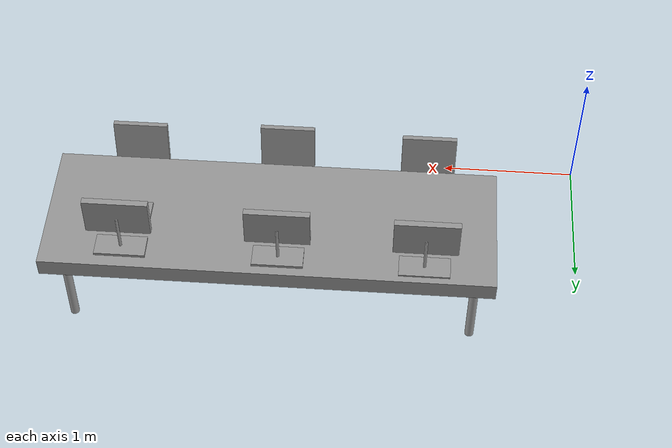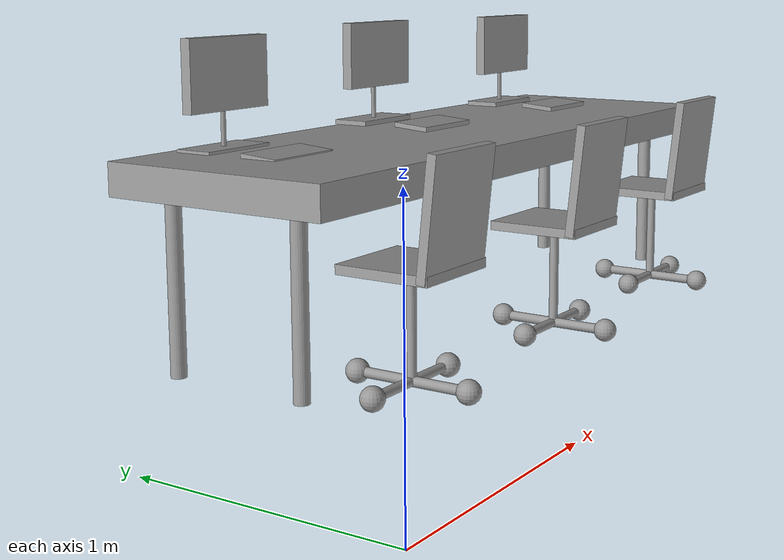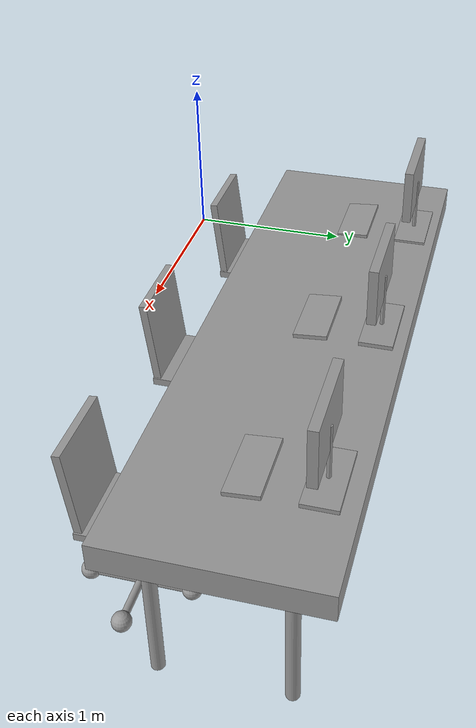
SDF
<?xml version='1.0'?>
<sdf version='1.6'>
  <model name='bancata'>
    <link name='link'>
      <inertial>
        <mass>0.00278324</mass>
        <inertia>
          <ixx>0.00011088</ixx>
          <ixy>0</ixy>
          <ixz>0</ixz>
          <iyy>0.00011088</iyy>
          <iyz>0</iyz>
          <izz>1.4e-06</izz>
        </inertia>
        <pose frame=''>0 0 0 0 -0 0</pose>
      </inertial>
      <self_collide>0</self_collide>
      <enable_wind>0</enable_wind>
      <kinematic>0</kinematic>
      <pose frame=''>0.8 1 0.357402 0 -0 0</pose>
      <gravity>1</gravity>
      <visual name='visual'>
        <geometry>
          <cylinder>
            <radius>0.0317717</radius>
            <length>0.689213</length>
          </cylinder>
        </geometry>
        <material>
          <script>
            <name>Gazebo/Grey</name>
            <uri>file://media/materials/scripts/gazebo.material</uri>
          </script>
          <shader type='vertex'>
            <normal_map>__default__</normal_map>
          </shader>
          <ambient>0.3 0.3 0.3 1</ambient>
          <diffuse>0.7 0.7 0.7 1</diffuse>
          <specular>0.01 0.01 0.01 1</specular>
          <emissive>0 0 0 1</emissive>
        </material>
        <pose frame=''>0 0 0 0 -0 0</pose>
        <transparency>0</transparency>
        <cast_shadows>1</cast_shadows>
      </visual>
      <collision name='collision'>
        <laser_retro>0</laser_retro>
        <max_contacts>10</max_contacts>
        <pose frame=''>0 0 0 0 -0 0</pose>
        <geometry>
          <cylinder>
            <radius>0.031772</radius>
            <length>0.689213</length>
          </cylinder>
        </geometry>
        <surface>
          <friction>
            <ode>
              <mu>1</mu>
              <mu2>1</mu2>
              <fdir1>0 0 0</fdir1>
              <slip1>0</slip1>
              <slip2>0</slip2>
            </ode>
            <torsional>
              <coefficient>1</coefficient>
              <patch_radius>0</patch_radius>
              <surface_radius>0</surface_radius>
              <use_patch_radius>1</use_patch_radius>
              <ode>
                <slip>0</slip>
              </ode>
            </torsional>
          </friction>
          <bounce>
            <restitution_coefficient>0</restitution_coefficient>
            <threshold>1e+06</threshold>
          </bounce>
          <contact>
            <collide_without_contact>0</collide_without_contact>
            <collide_without_contact_bitmask>1</collide_without_contact_bitmask>
            <collide_bitmask>1</collide_bitmask>
            <ode>
              <soft_cfm>0</soft_cfm>
              <soft_erp>0.2</soft_erp>
              <kp>1e+13</kp>
              <kd>1</kd>
              <max_vel>0.01</max_vel>
              <min_depth>0</min_depth>
            </ode>
            <bullet>
              <split_impulse>1</split_impulse>
              <split_impulse_penetration_threshold>-0.01</split_impulse_penetration_threshold>
              <soft_cfm>0</soft_cfm>
              <soft_erp>0.2</soft_erp>
              <kp>1e+13</kp>
              <kd>1</kd>
            </bullet>
          </contact>
        </surface>
      </collision>
    </link>
    <link name='link_0'>
      <inertial>
        <mass>1.42902</mass>
        <inertia>
          <ixx>0.12128</ixx>
          <ixy>0</ixy>
          <ixz>0</ixz>
          <iyy>1.19184</iyy>
          <iyz>0</iyz>
          <izz>1.30873</izz>
        </inertia>
        <pose frame=''>0 0 0 0 -0 0</pose>
      </inertial>
      <pose frame=''>2.25 1.3 0.78 -3e-06 -4e-06 -0</pose>
      <gravity>1</gravity>
      <self_collide>0</self_collide>
      <kinematic>0</kinematic>
      <enable_wind>0</enable_wind>
      <visual name='visual'>
        <pose frame=''>0 0 0 0 -0 0</pose>
        <geometry>
          <box>
            <size>3.16067 1 0.135737</size>
          </box>
        </geometry>
        <material>
          <lighting>1</lighting>
          <script>
            <uri>file://media/materials/scripts/gazebo.material</uri>
            <name>Gazebo/Grey</name>
          </script>
          <shader type='vertex'>
            <normal_map>__default__</normal_map>
          </shader>
          <ambient>0.3 0.3 0.3 1</ambient>
          <diffuse>0.7 0.7 0.7 1</diffuse>
          <specular>0.01 0.01 0.01 1</specular>
          <emissive>0 0 0 1</emissive>
        </material>
        <transparency>0</transparency>
        <cast_shadows>1</cast_shadows>
      </visual>
      <collision name='collision'>
        <laser_retro>0</laser_retro>
        <max_contacts>10</max_contacts>
        <pose frame=''>0 0 0 0 -0 0</pose>
        <geometry>
          <box>
            <size>3.16067 1 0.135737</size>
          </box>
        </geometry>
        <surface>
          <friction>
            <ode>
              <mu>1</mu>
              <mu2>1</mu2>
              <fdir1>0 0 0</fdir1>
              <slip1>0</slip1>
              <slip2>0</slip2>
            </ode>
            <torsional>
              <coefficient>1</coefficient>
              <patch_radius>0</patch_radius>
              <surface_radius>0</surface_radius>
              <use_patch_radius>1</use_patch_radius>
              <ode>
                <slip>0</slip>
              </ode>
            </torsional>
          </friction>
          <bounce>
            <restitution_coefficient>0</restitution_coefficient>
            <threshold>1e+06</threshold>
          </bounce>
          <contact>
            <collide_without_contact>0</collide_without_contact>
            <collide_without_contact_bitmask>1</collide_without_contact_bitmask>
            <collide_bitmask>1</collide_bitmask>
            <ode>
              <soft_cfm>0</soft_cfm>
              <soft_erp>0.2</soft_erp>
              <kp>1e+13</kp>
              <kd>1</kd>
              <max_vel>0.01</max_vel>
              <min_depth>0</min_depth>
            </ode>
            <bullet>
              <split_impulse>1</split_impulse>
              <split_impulse_penetration_threshold>-0.01</split_impulse_penetration_threshold>
              <soft_cfm>0</soft_cfm>
              <soft_erp>0.2</soft_erp>
              <kp>1e+13</kp>
              <kd>1</kd>
            </bullet>
          </contact>
        </surface>
      </collision>
    </link>
    <link name='link_clone_1'>
      <inertial>
        <mass>0.00278324</mass>
        <inertia>
          <ixx>0.00011087</ixx>
          <ixy>0</ixy>
          <ixz>0</ixz>
          <iyy>0.00011087</iyy>
          <iyz>0</iyz>
          <izz>1.4e-06</izz>
        </inertia>
        <pose frame=''>0 0 0 0 -0 0</pose>
      </inertial>
      <self_collide>0</self_collide>
      <enable_wind>0</enable_wind>
      <kinematic>0</kinematic>
      <pose frame=''>3.7 1.6 0.357402 0 -0 0</pose>
      <gravity>1</gravity>
      <visual name='visual'>
        <geometry>
          <cylinder>
            <radius>0.0317717</radius>
            <length>0.689213</length>
          </cylinder>
        </geometry>
        <material>
          <script>
            <name>Gazebo/Grey</name>
            <uri>file://media/materials/scripts/gazebo.material</uri>
          </script>
          <shader type='vertex'>
            <normal_map>__default__</normal_map>
          </shader>
          <ambient>0.3 0.3 0.3 1</ambient>
          <diffuse>0.7 0.7 0.7 1</diffuse>
          <specular>0.01 0.01 0.01 1</specular>
          <emissive>0 0 0 1</emissive>
        </material>
        <pose frame=''>0 0 0 0 -0 0</pose>
        <transparency>0</transparency>
        <cast_shadows>1</cast_shadows>
      </visual>
      <collision name='collision'>
        <laser_retro>0</laser_retro>
        <max_contacts>10</max_contacts>
        <pose frame=''>0 0 0 0 -0 0</pose>
        <geometry>
          <cylinder>
            <radius>0.031772</radius>
            <length>0.689213</length>
          </cylinder>
        </geometry>
        <surface>
          <friction>
            <ode>
              <mu>1</mu>
              <mu2>1</mu2>
              <fdir1>0 0 0</fdir1>
              <slip1>0</slip1>
              <slip2>0</slip2>
            </ode>
            <torsional>
              <coefficient>1</coefficient>
              <patch_radius>0</patch_radius>
              <surface_radius>0</surface_radius>
              <use_patch_radius>1</use_patch_radius>
              <ode>
                <slip>0</slip>
              </ode>
            </torsional>
          </friction>
          <bounce>
            <restitution_coefficient>0</restitution_coefficient>
            <threshold>1e+06</threshold>
          </bounce>
          <contact>
            <collide_without_contact>0</collide_without_contact>
            <collide_without_contact_bitmask>1</collide_without_contact_bitmask>
            <collide_bitmask>1</collide_bitmask>
            <ode>
              <soft_cfm>0</soft_cfm>
              <soft_erp>0.2</soft_erp>
              <kp>1e+13</kp>
              <kd>1</kd>
              <max_vel>0.01</max_vel>
              <min_depth>0</min_depth>
            </ode>
            <bullet>
              <split_impulse>1</split_impulse>
              <split_impulse_penetration_threshold>-0.01</split_impulse_penetration_threshold>
              <soft_cfm>0</soft_cfm>
              <soft_erp>0.2</soft_erp>
              <kp>1e+13</kp>
              <kd>1</kd>
            </bullet>
          </contact>
        </surface>
      </collision>
    </link>
    <link name='link_clone_2'>
      <inertial>
        <mass>0.00278324</mass>
        <inertia>
          <ixx>0.00011087</ixx>
          <ixy>0</ixy>
          <ixz>0</ixz>
          <iyy>0.00011087</iyy>
          <iyz>0</iyz>
          <izz>1.4e-06</izz>
        </inertia>
        <pose frame=''>0 0 0 0 -0 0</pose>
      </inertial>
      <self_collide>0</self_collide>
      <enable_wind>0</enable_wind>
      <kinematic>0</kinematic>
      <pose frame=''>0.8 1.6 0.357402 0 -0 0</pose>
      <gravity>1</gravity>
      <visual name='visual'>
        <geometry>
          <cylinder>
            <radius>0.0317717</radius>
            <length>0.689213</length>
          </cylinder>
        </geometry>
        <material>
          <script>
            <name>Gazebo/Grey</name>
            <uri>file://media/materials/scripts/gazebo.material</uri>
          </script>
          <shader type='vertex'>
            <normal_map>__default__</normal_map>
          </shader>
          <ambient>0.3 0.3 0.3 1</ambient>
          <diffuse>0.7 0.7 0.7 1</diffuse>
          <specular>0.01 0.01 0.01 1</specular>
          <emissive>0 0 0 1</emissive>
        </material>
        <pose frame=''>0 0 0 0 -0 0</pose>
        <transparency>0</transparency>
        <cast_shadows>1</cast_shadows>
      </visual>
      <collision name='collision'>
        <laser_retro>0</laser_retro>
        <max_contacts>10</max_contacts>
        <pose frame=''>0 0 0 0 -0 0</pose>
        <geometry>
          <cylinder>
            <radius>0.031772</radius>
            <length>0.689213</length>
          </cylinder>
        </geometry>
        <surface>
          <friction>
            <ode>
              <mu>1</mu>
              <mu2>1</mu2>
              <fdir1>0 0 0</fdir1>
              <slip1>0</slip1>
              <slip2>0</slip2>
            </ode>
            <torsional>
              <coefficient>1</coefficient>
              <patch_radius>0</patch_radius>
              <surface_radius>0</surface_radius>
              <use_patch_radius>1</use_patch_radius>
              <ode>
                <slip>0</slip>
              </ode>
            </torsional>
          </friction>
          <bounce>
            <restitution_coefficient>0</restitution_coefficient>
            <threshold>1e+06</threshold>
          </bounce>
          <contact>
            <collide_without_contact>0</collide_without_contact>
            <collide_without_contact_bitmask>1</collide_without_contact_bitmask>
            <collide_bitmask>1</collide_bitmask>
            <ode>
              <soft_cfm>0</soft_cfm>
              <soft_erp>0.2</soft_erp>
              <kp>1e+13</kp>
              <kd>1</kd>
              <max_vel>0.01</max_vel>
              <min_depth>0</min_depth>
            </ode>
            <bullet>
              <split_impulse>1</split_impulse>
              <split_impulse_penetration_threshold>-0.01</split_impulse_penetration_threshold>
              <soft_cfm>0</soft_cfm>
              <soft_erp>0.2</soft_erp>
              <kp>1e+13</kp>
              <kd>1</kd>
            </bullet>
          </contact>
        </surface>
      </collision>
    </link>
    <link name='link_clone_2_clone'>
      <inertial>
        <mass>0.00278324</mass>
        <inertia>
          <ixx>0.00011087</ixx>
          <ixy>0</ixy>
          <ixz>0</ixz>
          <iyy>0.00011087</iyy>
          <iyz>0</iyz>
          <izz>1.4e-06</izz>
        </inertia>
        <pose frame=''>0 0 0 0 -0 0</pose>
      </inertial>
      <self_collide>0</self_collide>
      <enable_wind>0</enable_wind>
      <kinematic>0</kinematic>
      <pose frame=''>3.7 1 0.357402 0 -0 0</pose>
      <gravity>1</gravity>
      <visual name='visual'>
        <geometry>
          <cylinder>
            <radius>0.0317717</radius>
            <length>0.689213</length>
          </cylinder>
        </geometry>
        <material>
          <script>
            <name>Gazebo/Grey</name>
            <uri>file://media/materials/scripts/gazebo.material</uri>
          </script>
          <shader type='vertex'>
            <normal_map>__default__</normal_map>
          </shader>
          <ambient>0.3 0.3 0.3 1</ambient>
          <diffuse>0.7 0.7 0.7 1</diffuse>
          <specular>0.01 0.01 0.01 1</specular>
          <emissive>0 0 0 1</emissive>
        </material>
        <pose frame=''>0 0 0 0 -0 0</pose>
        <transparency>0</transparency>
        <cast_shadows>1</cast_shadows>
      </visual>
      <collision name='collision'>
        <laser_retro>0</laser_retro>
        <max_contacts>10</max_contacts>
        <pose frame=''>0 0 0 0 -0 0</pose>
        <geometry>
          <cylinder>
            <radius>0.031772</radius>
            <length>0.689213</length>
          </cylinder>
        </geometry>
        <surface>
          <friction>
            <ode>
              <mu>1</mu>
              <mu2>1</mu2>
              <fdir1>0 0 0</fdir1>
              <slip1>0</slip1>
              <slip2>0</slip2>
            </ode>
            <torsional>
              <coefficient>1</coefficient>
              <patch_radius>0</patch_radius>
              <surface_radius>0</surface_radius>
              <use_patch_radius>1</use_patch_radius>
              <ode>
                <slip>0</slip>
              </ode>
            </torsional>
          </friction>
          <bounce>
            <restitution_coefficient>0</restitution_coefficient>
            <threshold>1e+06</threshold>
          </bounce>
          <contact>
            <collide_without_contact>0</collide_without_contact>
            <collide_without_contact_bitmask>1</collide_without_contact_bitmask>
            <collide_bitmask>1</collide_bitmask>
            <ode>
              <soft_cfm>0</soft_cfm>
              <soft_erp>0.2</soft_erp>
              <kp>1e+13</kp>
              <kd>1</kd>
              <max_vel>0.01</max_vel>
              <min_depth>0</min_depth>
            </ode>
            <bullet>
              <split_impulse>1</split_impulse>
              <split_impulse_penetration_threshold>-0.01</split_impulse_penetration_threshold>
              <soft_cfm>0</soft_cfm>
              <soft_erp>0.2</soft_erp>
              <kp>1e+13</kp>
              <kd>1</kd>
            </bullet>
          </contact>
        </surface>
      </collision>
    </link>
    <model name='Sedia'>
      <link name='link'>
        <inertial>
          <mass>1</mass>
          <inertia>
            <ixx>0.1</ixx>
            <ixy>0</ixy>
            <ixz>0</ixz>
            <iyy>0.1</iyy>
            <iyz>0</iyz>
            <izz>0.1</izz>
          </inertia>
          <pose frame=''>0 -0.05 0 0 -0 0</pose>
        </inertial>
        <self_collide>0</self_collide>
        <enable_wind>0</enable_wind>
        <kinematic>0</kinematic>
        <pose frame=''>0 -0.05 0.04 0 -0 0</pose>
        <gravity>1</gravity>
        <visual name='visual'>
          <geometry>
            <sphere>
              <radius>0.0479725</radius>
            </sphere>
          </geometry>
          <material>
            <script>
              <name>Gazebo/Grey</name>
              <uri>file://media/materials/scripts/gazebo.material</uri>
            </script>
            <shader type='vertex'>
              <normal_map>__default__</normal_map>
            </shader>
            <ambient>0.3 0.3 0.3 1</ambient>
            <diffuse>0.7 0.7 0.7 1</diffuse>
            <specular>0.01 0.01 0.01 1</specular>
            <emissive>0 0 0 1</emissive>
          </material>
          <pose frame=''>0 0 0 0 -0 0</pose>
          <transparency>0</transparency>
          <cast_shadows>1</cast_shadows>
        </visual>
        <collision name='collision'>
          <laser_retro>0</laser_retro>
          <max_contacts>10</max_contacts>
          <pose frame=''>0 0 0 0 -0 0</pose>
          <geometry>
            <sphere>
              <radius>0.047973</radius>
            </sphere>
          </geometry>
          <surface>
            <friction>
              <ode>
                <mu>1</mu>
                <mu2>1</mu2>
                <fdir1>0 0 0</fdir1>
                <slip1>0</slip1>
                <slip2>0</slip2>
              </ode>
              <torsional>
                <coefficient>1</coefficient>
                <patch_radius>0</patch_radius>
                <surface_radius>0</surface_radius>
                <use_patch_radius>1</use_patch_radius>
                <ode>
                  <slip>0</slip>
                </ode>
              </torsional>
            </friction>
            <bounce>
              <restitution_coefficient>0</restitution_coefficient>
              <threshold>1e+06</threshold>
            </bounce>
            <contact>
              <collide_without_contact>0</collide_without_contact>
              <collide_without_contact_bitmask>1</collide_without_contact_bitmask>
              <collide_bitmask>1</collide_bitmask>
              <ode>
                <soft_cfm>0</soft_cfm>
                <soft_erp>0.2</soft_erp>
                <kp>1e+13</kp>
                <kd>1</kd>
                <max_vel>0.01</max_vel>
                <min_depth>0</min_depth>
              </ode>
              <bullet>
                <split_impulse>1</split_impulse>
                <split_impulse_penetration_threshold>-0.01</split_impulse_penetration_threshold>
                <soft_cfm>0</soft_cfm>
                <soft_erp>0.2</soft_erp>
                <kp>1e+13</kp>
                <kd>1</kd>
              </bullet>
            </contact>
          </surface>
        </collision>
      </link>
      <link name='link_0'>
        <inertial>
          <mass>0.000595181</mass>
          <inertia>
            <ixx>8.34662e-06</ixx>
            <ixy>0</ixy>
            <ixz>0</ixz>
            <iyy>8.34662e-06</iyy>
            <iyz>0</iyz>
            <izz>1.11586e-07</izz>
          </inertia>
          <pose frame=''>0 0 0 0 -0 0</pose>
        </inertial>
        <pose frame=''>-0 0.2 0.2494 0 -0 0</pose>
        <gravity>1</gravity>
        <self_collide>0</self_collide>
        <kinematic>0</kinematic>
        <enable_wind>0</enable_wind>
        <visual name='visual'>
          <pose frame=''>0 0 0 0 -0 0</pose>
          <geometry>
            <cylinder>
              <radius>0.0193636</radius>
              <length>0.408851</length>
            </cylinder>
          </geometry>
          <material>
            <lighting>1</lighting>
            <script>
              <uri>file://media/materials/scripts/gazebo.material</uri>
              <name>Gazebo/Grey</name>
            </script>
            <shader type='vertex'>
              <normal_map>__default__</normal_map>
            </shader>
            <ambient>0.3 0.3 0.3 1</ambient>
            <diffuse>0.7 0.7 0.7 1</diffuse>
            <specular>0.01 0.01 0.01 1</specular>
            <emissive>0 0 0 1</emissive>
          </material>
          <transparency>0</transparency>
          <cast_shadows>1</cast_shadows>
        </visual>
        <collision name='collision'>
          <laser_retro>0</laser_retro>
          <max_contacts>10</max_contacts>
          <pose frame=''>0 0 0 0 -0 0</pose>
          <geometry>
            <cylinder>
              <radius>0.019364</radius>
              <length>0.408851</length>
            </cylinder>
          </geometry>
          <surface>
            <friction>
              <ode>
                <mu>1</mu>
                <mu2>1</mu2>
                <fdir1>0 0 0</fdir1>
                <slip1>0</slip1>
                <slip2>0</slip2>
              </ode>
              <torsional>
                <coefficient>1</coefficient>
                <patch_radius>0</patch_radius>
                <surface_radius>0</surface_radius>
                <use_patch_radius>1</use_patch_radius>
                <ode>
                  <slip>0</slip>
                </ode>
              </torsional>
            </friction>
            <bounce>
              <restitution_coefficient>0</restitution_coefficient>
              <threshold>1e+06</threshold>
            </bounce>
            <contact>
              <collide_without_contact>0</collide_without_contact>
              <collide_without_contact_bitmask>1</collide_without_contact_bitmask>
              <collide_bitmask>1</collide_bitmask>
              <ode>
                <soft_cfm>0</soft_cfm>
                <soft_erp>0.2</soft_erp>
                <kp>1e+13</kp>
                <kd>1</kd>
                <max_vel>0.01</max_vel>
                <min_depth>0</min_depth>
              </ode>
              <bullet>
                <split_impulse>1</split_impulse>
                <split_impulse_penetration_threshold>-0.01</split_impulse_penetration_threshold>
                <soft_cfm>0</soft_cfm>
                <soft_erp>0.2</soft_erp>
                <kp>1e+13</kp>
                <kd>1</kd>
              </bullet>
            </contact>
          </surface>
        </collision>
      </link>
      <link name='link_0_clone'>
        <inertial>
          <mass>0.000698061</mass>
          <inertia>
            <ixx>1.02332e-05</ixx>
            <ixy>0</ixy>
            <ixz>0</ixz>
            <iyy>1.02332e-05</iyy>
            <iyz>0</iyz>
            <izz>1.50251e-07</izz>
          </inertia>
          <pose frame=''>0 0 0 0 -0 0</pose>
        </inertial>
        <pose frame=''>0 0.2 0.04 -1.571 -0 0</pose>
        <gravity>1</gravity>
        <self_collide>0</self_collide>
        <kinematic>0</kinematic>
        <enable_wind>0</enable_wind>
        <visual name='visual'>
          <pose frame=''>0 0 0 0 -0 0</pose>
          <geometry>
            <cylinder>
              <radius>0.0207471</radius>
              <length>0.417878</length>
            </cylinder>
          </geometry>
          <material>
            <lighting>1</lighting>
            <script>
              <uri>file://media/materials/scripts/gazebo.material</uri>
              <name>Gazebo/Grey</name>
            </script>
            <shader type='vertex'>
              <normal_map>__default__</normal_map>
            </shader>
            <ambient>0.3 0.3 0.3 1</ambient>
            <diffuse>0.7 0.7 0.7 1</diffuse>
            <specular>0.01 0.01 0.01 1</specular>
            <emissive>0 0 0 1</emissive>
          </material>
          <transparency>0</transparency>
          <cast_shadows>1</cast_shadows>
        </visual>
        <collision name='collision'>
          <laser_retro>0</laser_retro>
          <max_contacts>10</max_contacts>
          <pose frame=''>0 0 0 0 -0 0</pose>
          <geometry>
            <cylinder>
              <radius>0.020748</radius>
              <length>0.417878</length>
            </cylinder>
          </geometry>
          <surface>
            <friction>
              <ode>
                <mu>1</mu>
                <mu2>1</mu2>
                <fdir1>0 0 0</fdir1>
                <slip1>0</slip1>
                <slip2>0</slip2>
              </ode>
              <torsional>
                <coefficient>1</coefficient>
                <patch_radius>0</patch_radius>
                <surface_radius>0</surface_radius>
                <use_patch_radius>1</use_patch_radius>
                <ode>
                  <slip>0</slip>
                </ode>
              </torsional>
            </friction>
            <bounce>
              <restitution_coefficient>0</restitution_coefficient>
              <threshold>1e+06</threshold>
            </bounce>
            <contact>
              <collide_without_contact>0</collide_without_contact>
              <collide_without_contact_bitmask>1</collide_without_contact_bitmask>
              <collide_bitmask>1</collide_bitmask>
              <ode>
                <soft_cfm>0</soft_cfm>
                <soft_erp>0.2</soft_erp>
                <kp>1e+13</kp>
                <kd>1</kd>
                <max_vel>0.01</max_vel>
                <min_depth>0</min_depth>
              </ode>
              <bullet>
                <split_impulse>1</split_impulse>
                <split_impulse_penetration_threshold>-0.01</split_impulse_penetration_threshold>
                <soft_cfm>0</soft_cfm>
                <soft_erp>0.2</soft_erp>
                <kp>1e+13</kp>
                <kd>1</kd>
              </bullet>
            </contact>
          </surface>
        </collision>
      </link>
      <link name='link_0_clone_0'>
        <inertial>
          <mass>0.00059327</mass>
          <inertia>
            <ixx>8.26633e-06</ixx>
            <ixy>0</ixy>
            <ixz>0</ixz>
            <iyy>8.26633e-06</iyy>
            <iyz>0</iyz>
            <izz>1.11228e-07</izz>
          </inertia>
          <pose frame=''>0 0 0 0 -0 0</pose>
        </inertial>
        <pose frame=''>0 0.2 0.04 0 -1.57059 0</pose>
        <gravity>1</gravity>
        <self_collide>0</self_collide>
        <kinematic>0</kinematic>
        <enable_wind>0</enable_wind>
        <visual name='visual'>
          <pose frame=''>0 0 0 0 -0 0</pose>
          <geometry>
            <cylinder>
              <radius>0.0193636</radius>
              <length>0.407525</length>
            </cylinder>
          </geometry>
          <material>
            <lighting>1</lighting>
            <script>
              <uri>file://media/materials/scripts/gazebo.material</uri>
              <name>Gazebo/Grey</name>
            </script>
            <shader type='vertex'>
              <normal_map>__default__</normal_map>
            </shader>
            <ambient>0.3 0.3 0.3 1</ambient>
            <diffuse>0.7 0.7 0.7 1</diffuse>
            <specular>0.01 0.01 0.01 1</specular>
            <emissive>0 0 0 1</emissive>
          </material>
          <transparency>0</transparency>
          <cast_shadows>1</cast_shadows>
        </visual>
        <collision name='collision'>
          <laser_retro>0</laser_retro>
          <max_contacts>10</max_contacts>
          <pose frame=''>0 0 0 0 -0 0</pose>
          <geometry>
            <cylinder>
              <radius>0.019364</radius>
              <length>0.407525</length>
            </cylinder>
          </geometry>
          <surface>
            <friction>
              <ode>
                <mu>1</mu>
                <mu2>1</mu2>
                <fdir1>0 0 0</fdir1>
                <slip1>0</slip1>
                <slip2>0</slip2>
              </ode>
              <torsional>
                <coefficient>1</coefficient>
                <patch_radius>0</patch_radius>
                <surface_radius>0</surface_radius>
                <use_patch_radius>1</use_patch_radius>
                <ode>
                  <slip>0</slip>
                </ode>
              </torsional>
            </friction>
            <bounce>
              <restitution_coefficient>0</restitution_coefficient>
              <threshold>1e+06</threshold>
            </bounce>
            <contact>
              <collide_without_contact>0</collide_without_contact>
              <collide_without_contact_bitmask>1</collide_without_contact_bitmask>
              <collide_bitmask>1</collide_bitmask>
              <ode>
                <soft_cfm>0</soft_cfm>
                <soft_erp>0.2</soft_erp>
                <kp>1e+13</kp>
                <kd>1</kd>
                <max_vel>0.01</max_vel>
                <min_depth>0</min_depth>
              </ode>
              <bullet>
                <split_impulse>1</split_impulse>
                <split_impulse_penetration_threshold>-0.01</split_impulse_penetration_threshold>
                <soft_cfm>0</soft_cfm>
                <soft_erp>0.2</soft_erp>
                <kp>1e+13</kp>
                <kd>1</kd>
              </bullet>
            </contact>
          </surface>
        </collision>
      </link>
      <link name='link_1'>
        <inertial>
          <mass>0.00616304</mass>
          <inertia>
            <ixx>8.379e-05</ixx>
            <ixy>0</ixy>
            <ixz>0</ixz>
            <iyy>8.148e-05</iyy>
            <iyz>0</iyz>
            <izz>0.00016374</izz>
          </inertia>
          <pose frame=''>0 0 0 0 -0 0</pose>
        </inertial>
        <pose frame=''>-0 0.2 0.48 0 -0 0</pose>
        <gravity>1</gravity>
        <self_collide>0</self_collide>
        <kinematic>0</kinematic>
        <enable_wind>0</enable_wind>
        <visual name='visual'>
          <pose frame=''>0 0 0 0 -0 0</pose>
          <geometry>
            <box>
              <size>0.396445 0.402068 0.038566</size>
            </box>
          </geometry>
          <material>
            <lighting>1</lighting>
            <script>
              <uri>file://media/materials/scripts/gazebo.material</uri>
              <name>Gazebo/Grey</name>
            </script>
            <shader type='vertex'>
              <normal_map>__default__</normal_map>
            </shader>
            <ambient>0.3 0.3 0.3 1</ambient>
            <diffuse>0.7 0.7 0.7 1</diffuse>
            <specular>0.01 0.01 0.01 1</specular>
            <emissive>0 0 0 1</emissive>
          </material>
          <transparency>0</transparency>
          <cast_shadows>1</cast_shadows>
        </visual>
        <collision name='collision'>
          <laser_retro>0</laser_retro>
          <max_contacts>10</max_contacts>
          <pose frame=''>0 0 0 0 -0 0</pose>
          <geometry>
            <box>
              <size>0.396445 0.402068 0.038566</size>
            </box>
          </geometry>
          <surface>
            <friction>
              <ode>
                <mu>1</mu>
                <mu2>1</mu2>
                <fdir1>0 0 0</fdir1>
                <slip1>0</slip1>
                <slip2>0</slip2>
              </ode>
              <torsional>
                <coefficient>1</coefficient>
                <patch_radius>0</patch_radius>
                <surface_radius>0</surface_radius>
                <use_patch_radius>1</use_patch_radius>
                <ode>
                  <slip>0</slip>
                </ode>
              </torsional>
            </friction>
            <bounce>
              <restitution_coefficient>0</restitution_coefficient>
              <threshold>1e+06</threshold>
            </bounce>
            <contact>
              <collide_without_contact>0</collide_without_contact>
              <collide_without_contact_bitmask>1</collide_without_contact_bitmask>
              <collide_bitmask>1</collide_bitmask>
              <ode>
                <soft_cfm>0</soft_cfm>
                <soft_erp>0.2</soft_erp>
                <kp>1e+13</kp>
                <kd>1</kd>
                <max_vel>0.01</max_vel>
                <min_depth>0</min_depth>
              </ode>
              <bullet>
                <split_impulse>1</split_impulse>
                <split_impulse_penetration_threshold>-0.01</split_impulse_penetration_threshold>
                <soft_cfm>0</soft_cfm>
                <soft_erp>0.2</soft_erp>
                <kp>1e+13</kp>
                <kd>1</kd>
              </bullet>
            </contact>
          </surface>
        </collision>
      </link>
      <link name='link_1_clone'>
        <inertial>
          <mass>0.0072018</mass>
          <inertia>
            <ixx>0.000133376</ixx>
            <ixy>0</ixy>
            <ixz>0</ixz>
            <iyy>9.52174e-05</iyy>
            <iyz>0</iyz>
            <izz>0.000226808</izz>
          </inertia>
          <pose frame=''>0 0 0 0 -0 0</pose>
        </inertial>
        <pose frame=''>-0.008803 -0.002064 0.701044 1.67698 -0 0</pose>
        <gravity>1</gravity>
        <self_collide>0</self_collide>
        <kinematic>0</kinematic>
        <enable_wind>0</enable_wind>
        <visual name='visual'>
          <pose frame=''>0 0 0 0 -0 0</pose>
          <geometry>
            <box>
              <size>0.396445 0.46984 0.038566</size>
            </box>
          </geometry>
          <material>
            <lighting>1</lighting>
            <script>
              <uri>file://media/materials/scripts/gazebo.material</uri>
              <name>Gazebo/Grey</name>
            </script>
            <shader type='vertex'>
              <normal_map>__default__</normal_map>
            </shader>
            <ambient>0.3 0.3 0.3 1</ambient>
            <diffuse>0.7 0.7 0.7 1</diffuse>
            <specular>0.01 0.01 0.01 1</specular>
            <emissive>0 0 0 1</emissive>
          </material>
          <transparency>0</transparency>
          <cast_shadows>1</cast_shadows>
        </visual>
        <collision name='collision'>
          <laser_retro>0</laser_retro>
          <max_contacts>10</max_contacts>
          <pose frame=''>0 0 0 0 -0 0</pose>
          <geometry>
            <box>
              <size>0.396445 0.46984 0.038566</size>
            </box>
          </geometry>
          <surface>
            <friction>
              <ode>
                <mu>1</mu>
                <mu2>1</mu2>
                <fdir1>0 0 0</fdir1>
                <slip1>0</slip1>
                <slip2>0</slip2>
              </ode>
              <torsional>
                <coefficient>1</coefficient>
                <patch_radius>0</patch_radius>
                <surface_radius>0</surface_radius>
                <use_patch_radius>1</use_patch_radius>
                <ode>
                  <slip>0</slip>
                </ode>
              </torsional>
            </friction>
            <bounce>
              <restitution_coefficient>0</restitution_coefficient>
              <threshold>1e+06</threshold>
            </bounce>
            <contact>
              <collide_without_contact>0</collide_without_contact>
              <collide_without_contact_bitmask>1</collide_without_contact_bitmask>
              <collide_bitmask>1</collide_bitmask>
              <ode>
                <soft_cfm>0</soft_cfm>
                <soft_erp>0.2</soft_erp>
                <kp>1e+13</kp>
                <kd>1</kd>
                <max_vel>0.01</max_vel>
                <min_depth>0</min_depth>
              </ode>
              <bullet>
                <split_impulse>1</split_impulse>
                <split_impulse_penetration_threshold>-0.01</split_impulse_penetration_threshold>
                <soft_cfm>0</soft_cfm>
                <soft_erp>0.2</soft_erp>
                <kp>1e+13</kp>
                <kd>1</kd>
              </bullet>
            </contact>
          </surface>
        </collision>
      </link>
      <link name='link_clone'>
        <inertial>
          <mass>1</mass>
          <inertia>
            <ixx>0.1</ixx>
            <ixy>0</ixy>
            <ixz>0</ixz>
            <iyy>0.1</iyy>
            <iyz>0</iyz>
            <izz>0.1</izz>
          </inertia>
          <pose frame=''>0 0 0.04 0 -0 0</pose>
        </inertial>
        <self_collide>0</self_collide>
        <enable_wind>0</enable_wind>
        <kinematic>0</kinematic>
        <pose frame=''>0.25 0.2 0.04 0 -0 0</pose>
        <gravity>1</gravity>
        <visual name='visual'>
          <geometry>
            <sphere>
              <radius>0.0479725</radius>
            </sphere>
          </geometry>
          <material>
            <script>
              <name>Gazebo/Grey</name>
              <uri>file://media/materials/scripts/gazebo.material</uri>
            </script>
            <shader type='vertex'>
              <normal_map>__default__</normal_map>
            </shader>
            <ambient>0.3 0.3 0.3 1</ambient>
            <diffuse>0.7 0.7 0.7 1</diffuse>
            <specular>0.01 0.01 0.01 1</specular>
            <emissive>0 0 0 1</emissive>
          </material>
          <pose frame=''>0 0 0 0 -0 0</pose>
          <transparency>0</transparency>
          <cast_shadows>1</cast_shadows>
        </visual>
        <collision name='collision'>
          <laser_retro>0</laser_retro>
          <max_contacts>10</max_contacts>
          <pose frame=''>0 0 0 0 -0 0</pose>
          <geometry>
            <sphere>
              <radius>0.047973</radius>
            </sphere>
          </geometry>
          <surface>
            <friction>
              <ode>
                <mu>1</mu>
                <mu2>1</mu2>
                <fdir1>0 0 0</fdir1>
                <slip1>0</slip1>
                <slip2>0</slip2>
              </ode>
              <torsional>
                <coefficient>1</coefficient>
                <patch_radius>0</patch_radius>
                <surface_radius>0</surface_radius>
                <use_patch_radius>1</use_patch_radius>
                <ode>
                  <slip>0</slip>
                </ode>
              </torsional>
            </friction>
            <bounce>
              <restitution_coefficient>0</restitution_coefficient>
              <threshold>1e+06</threshold>
            </bounce>
            <contact>
              <collide_without_contact>0</collide_without_contact>
              <collide_without_contact_bitmask>1</collide_without_contact_bitmask>
              <collide_bitmask>1</collide_bitmask>
              <ode>
                <soft_cfm>0</soft_cfm>
                <soft_erp>0.2</soft_erp>
                <kp>1e+13</kp>
                <kd>1</kd>
                <max_vel>0.01</max_vel>
                <min_depth>0</min_depth>
              </ode>
              <bullet>
                <split_impulse>1</split_impulse>
                <split_impulse_penetration_threshold>-0.01</split_impulse_penetration_threshold>
                <soft_cfm>0</soft_cfm>
                <soft_erp>0.2</soft_erp>
                <kp>1e+13</kp>
                <kd>1</kd>
              </bullet>
            </contact>
          </surface>
        </collision>
      </link>
      <link name='link_clone_0'>
        <inertial>
          <mass>1</mass>
          <inertia>
            <ixx>0.1</ixx>
            <ixy>0</ixy>
            <ixz>0</ixz>
            <iyy>0.1</iyy>
            <iyz>0</iyz>
            <izz>0.1</izz>
          </inertia>
          <pose frame=''>0 0 0 0 -0 0</pose>
        </inertial>
        <self_collide>0</self_collide>
        <enable_wind>0</enable_wind>
        <kinematic>0</kinematic>
        <pose frame=''>-0 0.45 0.04 0 -0 0</pose>
        <gravity>1</gravity>
        <visual name='visual'>
          <geometry>
            <sphere>
              <radius>0.0479725</radius>
            </sphere>
          </geometry>
          <material>
            <script>
              <name>Gazebo/Grey</name>
              <uri>file://media/materials/scripts/gazebo.material</uri>
            </script>
            <shader type='vertex'>
              <normal_map>__default__</normal_map>
            </shader>
            <ambient>0.3 0.3 0.3 1</ambient>
            <diffuse>0.7 0.7 0.7 1</diffuse>
            <specular>0.01 0.01 0.01 1</specular>
            <emissive>0 0 0 1</emissive>
          </material>
          <pose frame=''>0 0 0 0 -0 0</pose>
          <transparency>0</transparency>
          <cast_shadows>1</cast_shadows>
        </visual>
        <collision name='collision'>
          <laser_retro>0</laser_retro>
          <max_contacts>10</max_contacts>
          <pose frame=''>0 0 0 0 -0 0</pose>
          <geometry>
            <sphere>
              <radius>0.047973</radius>
            </sphere>
          </geometry>
          <surface>
            <friction>
              <ode>
                <mu>1</mu>
                <mu2>1</mu2>
                <fdir1>0 0 0</fdir1>
                <slip1>0</slip1>
                <slip2>0</slip2>
              </ode>
              <torsional>
                <coefficient>1</coefficient>
                <patch_radius>0</patch_radius>
                <surface_radius>0</surface_radius>
                <use_patch_radius>1</use_patch_radius>
                <ode>
                  <slip>0</slip>
                </ode>
              </torsional>
            </friction>
            <bounce>
              <restitution_coefficient>0</restitution_coefficient>
              <threshold>1e+06</threshold>
            </bounce>
            <contact>
              <collide_without_contact>0</collide_without_contact>
              <collide_without_contact_bitmask>1</collide_without_contact_bitmask>
              <collide_bitmask>1</collide_bitmask>
              <ode>
                <soft_cfm>0</soft_cfm>
                <soft_erp>0.2</soft_erp>
                <kp>1e+13</kp>
                <kd>1</kd>
                <max_vel>0.01</max_vel>
                <min_depth>0</min_depth>
              </ode>
              <bullet>
                <split_impulse>1</split_impulse>
                <split_impulse_penetration_threshold>-0.01</split_impulse_penetration_threshold>
                <soft_cfm>0</soft_cfm>
                <soft_erp>0.2</soft_erp>
                <kp>1e+13</kp>
                <kd>1</kd>
              </bullet>
            </contact>
          </surface>
        </collision>
      </link>
      <link name='link_clone_1'>
        <inertial>
          <mass>1</mass>
          <inertia>
            <ixx>0.1</ixx>
            <ixy>0</ixy>
            <ixz>0</ixz>
            <iyy>0.1</iyy>
            <iyz>0</iyz>
            <izz>0.1</izz>
          </inertia>
          <pose frame=''>0 0 0 0 -0 0</pose>
        </inertial>
        <self_collide>0</self_collide>
        <enable_wind>0</enable_wind>
        <kinematic>0</kinematic>
        <pose frame=''>-0.25 0.2 0.04 0 -0 0</pose>
        <gravity>1</gravity>
        <visual name='visual'>
          <geometry>
            <sphere>
              <radius>0.0479725</radius>
            </sphere>
          </geometry>
          <material>
            <script>
              <name>Gazebo/Grey</name>
              <uri>file://media/materials/scripts/gazebo.material</uri>
            </script>
            <shader type='vertex'>
              <normal_map>__default__</normal_map>
            </shader>
            <ambient>0.3 0.3 0.3 1</ambient>
            <diffuse>0.7 0.7 0.7 1</diffuse>
            <specular>0.01 0.01 0.01 1</specular>
            <emissive>0 0 0 1</emissive>
          </material>
          <pose frame=''>0 0 0 0 -0 0</pose>
          <transparency>0</transparency>
          <cast_shadows>1</cast_shadows>
        </visual>
        <collision name='collision'>
          <laser_retro>0</laser_retro>
          <max_contacts>10</max_contacts>
          <pose frame=''>0 0 0 0 -0 0</pose>
          <geometry>
            <sphere>
              <radius>0.047973</radius>
            </sphere>
          </geometry>
          <surface>
            <friction>
              <ode>
                <mu>1</mu>
                <mu2>1</mu2>
                <fdir1>0 0 0</fdir1>
                <slip1>0</slip1>
                <slip2>0</slip2>
              </ode>
              <torsional>
                <coefficient>1</coefficient>
                <patch_radius>0</patch_radius>
                <surface_radius>0</surface_radius>
                <use_patch_radius>1</use_patch_radius>
                <ode>
                  <slip>0</slip>
                </ode>
              </torsional>
            </friction>
            <bounce>
              <restitution_coefficient>0</restitution_coefficient>
              <threshold>1e+06</threshold>
            </bounce>
            <contact>
              <collide_without_contact>0</collide_without_contact>
              <collide_without_contact_bitmask>1</collide_without_contact_bitmask>
              <collide_bitmask>1</collide_bitmask>
              <ode>
                <soft_cfm>0</soft_cfm>
                <soft_erp>0.2</soft_erp>
                <kp>1e+13</kp>
                <kd>1</kd>
                <max_vel>0.01</max_vel>
                <min_depth>0</min_depth>
              </ode>
              <bullet>
                <split_impulse>1</split_impulse>
                <split_impulse_penetration_threshold>-0.01</split_impulse_penetration_threshold>
                <soft_cfm>0</soft_cfm>
                <soft_erp>0.2</soft_erp>
                <kp>1e+13</kp>
                <kd>1</kd>
              </bullet>
            </contact>
          </surface>
        </collision>
      </link>
      <joint name='link_0_clone_0_JOINT_1' type='fixed'>
        <parent>link_0_clone_0</parent>
        <child>link_clone</child>
        <pose frame=''>0 0 0 0 -0 0</pose>
        <physics>
          <ode>
            <limit>
              <cfm>0</cfm>
              <erp>0.2</erp>
            </limit>
            <suspension>
              <cfm>0</cfm>
              <erp>0.2</erp>
            </suspension>
          </ode>
        </physics>
      </joint>
      <joint name='link_0_clone_0_JOINT_2' type='fixed'>
        <parent>link_0_clone_0</parent>
        <child>link_clone_1</child>
        <pose frame=''>0 0 0 0 -0 0</pose>
        <physics>
          <ode>
            <limit>
              <cfm>0</cfm>
              <erp>0.2</erp>
            </limit>
            <suspension>
              <cfm>0</cfm>
              <erp>0.2</erp>
            </suspension>
          </ode>
        </physics>
      </joint>
      <joint name='link_0_clone_JOINT_3' type='fixed'>
        <parent>link_0_clone</parent>
        <child>link_clone_0</child>
        <pose frame=''>0 0 0 0 -0 0</pose>
        <physics>
          <ode>
            <limit>
              <cfm>0</cfm>
              <erp>0.2</erp>
            </limit>
            <suspension>
              <cfm>0</cfm>
              <erp>0.2</erp>
            </suspension>
          </ode>
        </physics>
      </joint>
      <joint name='link_0_clone_JOINT_4' type='fixed'>
        <parent>link_0_clone</parent>
        <child>link</child>
        <pose frame=''>0 0 0 0 -0 0</pose>
        <physics>
          <ode>
            <limit>
              <cfm>0</cfm>
              <erp>0.2</erp>
            </limit>
            <suspension>
              <cfm>0</cfm>
              <erp>0.2</erp>
            </suspension>
          </ode>
        </physics>
      </joint>
      <joint name='link_1_JOINT_0' type='fixed'>
        <parent>link_1</parent>
        <child>link_1_clone</child>
        <pose frame=''>0 0 0 0 -0 0</pose>
        <physics>
          <ode>
            <limit>
              <cfm>0</cfm>
              <erp>0.2</erp>
            </limit>
            <suspension>
              <cfm>0</cfm>
              <erp>0.2</erp>
            </suspension>
          </ode>
        </physics>
      </joint>
      <joint name='link_1_JOINT_4' type='fixed'>
        <parent>link_1</parent>
        <child>link_0</child>
        <pose frame=''>0 0 0 0 -0 0</pose>
        <physics>
          <ode>
            <limit>
              <cfm>0</cfm>
              <erp>0.2</erp>
            </limit>
            <suspension>
              <cfm>0</cfm>
              <erp>0.2</erp>
            </suspension>
          </ode>
        </physics>
      </joint>
      <joint name='link_JOINT_3' type='fixed'>
        <parent>link</parent>
        <child>link_0</child>
        <pose frame=''>0 0 0 0 -0 0</pose>
        <physics>
          <ode>
            <limit>
              <cfm>0</cfm>
              <erp>0.2</erp>
            </limit>
            <suspension>
              <cfm>0</cfm>
              <erp>0.2</erp>
            </suspension>
          </ode>
        </physics>
      </joint>
      <joint name='link_clone_0_JOINT_0' type='fixed'>
        <parent>link_clone_0</parent>
        <child>link_0_LINK_FRAME_VISUAL___Y_AXIS</child>
        <pose frame=''>0 0 0 0 -0 0</pose>
        <physics>
          <ode>
            <limit>
              <cfm>0</cfm>
              <erp>0.2</erp>
            </limit>
            <suspension>
              <cfm>0</cfm>
              <erp>0.2</erp>
            </suspension>
          </ode>
        </physics>
      </joint>
      <joint name='link_clone_1_JOINT_2' type='fixed'>
        <parent>link_clone_1</parent>
        <child>link_0</child>
        <pose frame=''>0 0 0 0 -0 0</pose>
        <physics>
          <ode>
            <limit>
              <cfm>0</cfm>
              <erp>0.2</erp>
            </limit>
            <suspension>
              <cfm>0</cfm>
              <erp>0.2</erp>
            </suspension>
          </ode>
        </physics>
      </joint>
      <joint name='link_clone_JOINT_1' type='fixed'>
        <parent>link_clone</parent>
        <child>link_0</child>
        <pose frame=''>0 0 0 0 -0 0</pose>
        <physics>
          <ode>
            <limit>
              <cfm>0</cfm>
              <erp>0.2</erp>
            </limit>
            <suspension>
              <cfm>0</cfm>
              <erp>0.2</erp>
            </suspension>
          </ode>
        </physics>
      </joint>
      <static>0</static>
      <allow_auto_disable>1</allow_auto_disable>
      <pose frame=''>1.16662 0.572146 -0.001178 0 -0 0</pose>
    </model>
    <model name='Sedia_clone'>
      <link name='link'>
        <inertial>
          <mass>1</mass>
          <inertia>
            <ixx>0.1</ixx>
            <ixy>0</ixy>
            <ixz>0</ixz>
            <iyy>0.1</iyy>
            <iyz>0</iyz>
            <izz>0.1</izz>
          </inertia>
          <pose frame=''>0 -0.05 0 0 -0 0</pose>
        </inertial>
        <self_collide>0</self_collide>
        <enable_wind>0</enable_wind>
        <kinematic>0</kinematic>
        <pose frame=''>0 -0.05 0.04 0 -0 0</pose>
        <gravity>1</gravity>
        <visual name='visual'>
          <geometry>
            <sphere>
              <radius>0.0479725</radius>
            </sphere>
          </geometry>
          <material>
            <script>
              <name>Gazebo/Grey</name>
              <uri>file://media/materials/scripts/gazebo.material</uri>
            </script>
            <shader type='vertex'>
              <normal_map>__default__</normal_map>
            </shader>
            <ambient>0.3 0.3 0.3 1</ambient>
            <diffuse>0.7 0.7 0.7 1</diffuse>
            <specular>0.01 0.01 0.01 1</specular>
            <emissive>0 0 0 1</emissive>
          </material>
          <pose frame=''>0 0 0 0 -0 0</pose>
          <transparency>0</transparency>
          <cast_shadows>1</cast_shadows>
        </visual>
        <collision name='collision'>
          <laser_retro>0</laser_retro>
          <max_contacts>10</max_contacts>
          <pose frame=''>0 0 0 0 -0 0</pose>
          <geometry>
            <sphere>
              <radius>0.047973</radius>
            </sphere>
          </geometry>
          <surface>
            <friction>
              <ode>
                <mu>1</mu>
                <mu2>1</mu2>
                <fdir1>0 0 0</fdir1>
                <slip1>0</slip1>
                <slip2>0</slip2>
              </ode>
              <torsional>
                <coefficient>1</coefficient>
                <patch_radius>0</patch_radius>
                <surface_radius>0</surface_radius>
                <use_patch_radius>1</use_patch_radius>
                <ode>
                  <slip>0</slip>
                </ode>
              </torsional>
            </friction>
            <bounce>
              <restitution_coefficient>0</restitution_coefficient>
              <threshold>1e+06</threshold>
            </bounce>
            <contact>
              <collide_without_contact>0</collide_without_contact>
              <collide_without_contact_bitmask>1</collide_without_contact_bitmask>
              <collide_bitmask>1</collide_bitmask>
              <ode>
                <soft_cfm>0</soft_cfm>
                <soft_erp>0.2</soft_erp>
                <kp>1e+13</kp>
                <kd>1</kd>
                <max_vel>0.01</max_vel>
                <min_depth>0</min_depth>
              </ode>
              <bullet>
                <split_impulse>1</split_impulse>
                <split_impulse_penetration_threshold>-0.01</split_impulse_penetration_threshold>
                <soft_cfm>0</soft_cfm>
                <soft_erp>0.2</soft_erp>
                <kp>1e+13</kp>
                <kd>1</kd>
              </bullet>
            </contact>
          </surface>
        </collision>
      </link>
      <link name='link_0'>
        <inertial>
          <mass>0.000595181</mass>
          <inertia>
            <ixx>8.34662e-06</ixx>
            <ixy>0</ixy>
            <ixz>0</ixz>
            <iyy>8.34662e-06</iyy>
            <iyz>0</iyz>
            <izz>1.11586e-07</izz>
          </inertia>
          <pose frame=''>0 0 0 0 -0 0</pose>
        </inertial>
        <pose frame=''>-0 0.2 0.2494 0 -0 0</pose>
        <gravity>1</gravity>
        <self_collide>0</self_collide>
        <kinematic>0</kinematic>
        <enable_wind>0</enable_wind>
        <visual name='visual'>
          <pose frame=''>0 0 0 0 -0 0</pose>
          <geometry>
            <cylinder>
              <radius>0.0193636</radius>
              <length>0.408851</length>
            </cylinder>
          </geometry>
          <material>
            <lighting>1</lighting>
            <script>
              <uri>file://media/materials/scripts/gazebo.material</uri>
              <name>Gazebo/Grey</name>
            </script>
            <shader type='vertex'>
              <normal_map>__default__</normal_map>
            </shader>
            <ambient>0.3 0.3 0.3 1</ambient>
            <diffuse>0.7 0.7 0.7 1</diffuse>
            <specular>0.01 0.01 0.01 1</specular>
            <emissive>0 0 0 1</emissive>
          </material>
          <transparency>0</transparency>
          <cast_shadows>1</cast_shadows>
        </visual>
        <collision name='collision'>
          <laser_retro>0</laser_retro>
          <max_contacts>10</max_contacts>
          <pose frame=''>0 0 0 0 -0 0</pose>
          <geometry>
            <cylinder>
              <radius>0.019364</radius>
              <length>0.408851</length>
            </cylinder>
          </geometry>
          <surface>
            <friction>
              <ode>
                <mu>1</mu>
                <mu2>1</mu2>
                <fdir1>0 0 0</fdir1>
                <slip1>0</slip1>
                <slip2>0</slip2>
              </ode>
              <torsional>
                <coefficient>1</coefficient>
                <patch_radius>0</patch_radius>
                <surface_radius>0</surface_radius>
                <use_patch_radius>1</use_patch_radius>
                <ode>
                  <slip>0</slip>
                </ode>
              </torsional>
            </friction>
            <bounce>
              <restitution_coefficient>0</restitution_coefficient>
              <threshold>1e+06</threshold>
            </bounce>
            <contact>
              <collide_without_contact>0</collide_without_contact>
              <collide_without_contact_bitmask>1</collide_without_contact_bitmask>
              <collide_bitmask>1</collide_bitmask>
              <ode>
                <soft_cfm>0</soft_cfm>
                <soft_erp>0.2</soft_erp>
                <kp>1e+13</kp>
                <kd>1</kd>
                <max_vel>0.01</max_vel>
                <min_depth>0</min_depth>
              </ode>
              <bullet>
                <split_impulse>1</split_impulse>
                <split_impulse_penetration_threshold>-0.01</split_impulse_penetration_threshold>
                <soft_cfm>0</soft_cfm>
                <soft_erp>0.2</soft_erp>
                <kp>1e+13</kp>
                <kd>1</kd>
              </bullet>
            </contact>
          </surface>
        </collision>
      </link>
      <link name='link_0_clone'>
        <inertial>
          <mass>0.000698061</mass>
          <inertia>
            <ixx>1.02332e-05</ixx>
            <ixy>0</ixy>
            <ixz>0</ixz>
            <iyy>1.02332e-05</iyy>
            <iyz>0</iyz>
            <izz>1.50251e-07</izz>
          </inertia>
          <pose frame=''>0 0 0 0 -0 0</pose>
        </inertial>
        <pose frame=''>0 0.2 0.04 -1.571 -0 0</pose>
        <gravity>1</gravity>
        <self_collide>0</self_collide>
        <kinematic>0</kinematic>
        <enable_wind>0</enable_wind>
        <visual name='visual'>
          <pose frame=''>0 0 0 0 -0 0</pose>
          <geometry>
            <cylinder>
              <radius>0.0207471</radius>
              <length>0.417878</length>
            </cylinder>
          </geometry>
          <material>
            <lighting>1</lighting>
            <script>
              <uri>file://media/materials/scripts/gazebo.material</uri>
              <name>Gazebo/Grey</name>
            </script>
            <shader type='vertex'>
              <normal_map>__default__</normal_map>
            </shader>
            <ambient>0.3 0.3 0.3 1</ambient>
            <diffuse>0.7 0.7 0.7 1</diffuse>
            <specular>0.01 0.01 0.01 1</specular>
            <emissive>0 0 0 1</emissive>
          </material>
          <transparency>0</transparency>
          <cast_shadows>1</cast_shadows>
        </visual>
        <collision name='collision'>
          <laser_retro>0</laser_retro>
          <max_contacts>10</max_contacts>
          <pose frame=''>0 0 0 0 -0 0</pose>
          <geometry>
            <cylinder>
              <radius>0.020748</radius>
              <length>0.417878</length>
            </cylinder>
          </geometry>
          <surface>
            <friction>
              <ode>
                <mu>1</mu>
                <mu2>1</mu2>
                <fdir1>0 0 0</fdir1>
                <slip1>0</slip1>
                <slip2>0</slip2>
              </ode>
              <torsional>
                <coefficient>1</coefficient>
                <patch_radius>0</patch_radius>
                <surface_radius>0</surface_radius>
                <use_patch_radius>1</use_patch_radius>
                <ode>
                  <slip>0</slip>
                </ode>
              </torsional>
            </friction>
            <bounce>
              <restitution_coefficient>0</restitution_coefficient>
              <threshold>1e+06</threshold>
            </bounce>
            <contact>
              <collide_without_contact>0</collide_without_contact>
              <collide_without_contact_bitmask>1</collide_without_contact_bitmask>
              <collide_bitmask>1</collide_bitmask>
              <ode>
                <soft_cfm>0</soft_cfm>
                <soft_erp>0.2</soft_erp>
                <kp>1e+13</kp>
                <kd>1</kd>
                <max_vel>0.01</max_vel>
                <min_depth>0</min_depth>
              </ode>
              <bullet>
                <split_impulse>1</split_impulse>
                <split_impulse_penetration_threshold>-0.01</split_impulse_penetration_threshold>
                <soft_cfm>0</soft_cfm>
                <soft_erp>0.2</soft_erp>
                <kp>1e+13</kp>
                <kd>1</kd>
              </bullet>
            </contact>
          </surface>
        </collision>
      </link>
      <link name='link_0_clone_0'>
        <inertial>
          <mass>0.00059327</mass>
          <inertia>
            <ixx>8.26633e-06</ixx>
            <ixy>0</ixy>
            <ixz>0</ixz>
            <iyy>8.26633e-06</iyy>
            <iyz>0</iyz>
            <izz>1.11228e-07</izz>
          </inertia>
          <pose frame=''>0 0 0 0 -0 0</pose>
        </inertial>
        <pose frame=''>0 0.2 0.04 0 -1.57059 0</pose>
        <gravity>1</gravity>
        <self_collide>0</self_collide>
        <kinematic>0</kinematic>
        <enable_wind>0</enable_wind>
        <visual name='visual'>
          <pose frame=''>0 0 0 0 -0 0</pose>
          <geometry>
            <cylinder>
              <radius>0.0193636</radius>
              <length>0.407525</length>
            </cylinder>
          </geometry>
          <material>
            <lighting>1</lighting>
            <script>
              <uri>file://media/materials/scripts/gazebo.material</uri>
              <name>Gazebo/Grey</name>
            </script>
            <shader type='vertex'>
              <normal_map>__default__</normal_map>
            </shader>
            <ambient>0.3 0.3 0.3 1</ambient>
            <diffuse>0.7 0.7 0.7 1</diffuse>
            <specular>0.01 0.01 0.01 1</specular>
            <emissive>0 0 0 1</emissive>
          </material>
          <transparency>0</transparency>
          <cast_shadows>1</cast_shadows>
        </visual>
        <collision name='collision'>
          <laser_retro>0</laser_retro>
          <max_contacts>10</max_contacts>
          <pose frame=''>0 0 0 0 -0 0</pose>
          <geometry>
            <cylinder>
              <radius>0.019364</radius>
              <length>0.407525</length>
            </cylinder>
          </geometry>
          <surface>
            <friction>
              <ode>
                <mu>1</mu>
                <mu2>1</mu2>
                <fdir1>0 0 0</fdir1>
                <slip1>0</slip1>
                <slip2>0</slip2>
              </ode>
              <torsional>
                <coefficient>1</coefficient>
                <patch_radius>0</patch_radius>
                <surface_radius>0</surface_radius>
                <use_patch_radius>1</use_patch_radius>
                <ode>
                  <slip>0</slip>
                </ode>
              </torsional>
            </friction>
            <bounce>
              <restitution_coefficient>0</restitution_coefficient>
              <threshold>1e+06</threshold>
            </bounce>
            <contact>
              <collide_without_contact>0</collide_without_contact>
              <collide_without_contact_bitmask>1</collide_without_contact_bitmask>
              <collide_bitmask>1</collide_bitmask>
              <ode>
                <soft_cfm>0</soft_cfm>
                <soft_erp>0.2</soft_erp>
                <kp>1e+13</kp>
                <kd>1</kd>
                <max_vel>0.01</max_vel>
                <min_depth>0</min_depth>
              </ode>
              <bullet>
                <split_impulse>1</split_impulse>
                <split_impulse_penetration_threshold>-0.01</split_impulse_penetration_threshold>
                <soft_cfm>0</soft_cfm>
                <soft_erp>0.2</soft_erp>
                <kp>1e+13</kp>
                <kd>1</kd>
              </bullet>
            </contact>
          </surface>
        </collision>
      </link>
      <link name='link_1'>
        <inertial>
          <mass>0.00616304</mass>
          <inertia>
            <ixx>8.379e-05</ixx>
            <ixy>0</ixy>
            <ixz>0</ixz>
            <iyy>8.148e-05</iyy>
            <iyz>0</iyz>
            <izz>0.00016374</izz>
          </inertia>
          <pose frame=''>0 0 0 0 -0 0</pose>
        </inertial>
        <pose frame=''>-0 0.2 0.48 0 -0 0</pose>
        <gravity>1</gravity>
        <self_collide>0</self_collide>
        <kinematic>0</kinematic>
        <enable_wind>0</enable_wind>
        <visual name='visual'>
          <pose frame=''>0 0 0 0 -0 0</pose>
          <geometry>
            <box>
              <size>0.396445 0.402068 0.038566</size>
            </box>
          </geometry>
          <material>
            <lighting>1</lighting>
            <script>
              <uri>file://media/materials/scripts/gazebo.material</uri>
              <name>Gazebo/Grey</name>
            </script>
            <shader type='vertex'>
              <normal_map>__default__</normal_map>
            </shader>
            <ambient>0.3 0.3 0.3 1</ambient>
            <diffuse>0.7 0.7 0.7 1</diffuse>
            <specular>0.01 0.01 0.01 1</specular>
            <emissive>0 0 0 1</emissive>
          </material>
          <transparency>0</transparency>
          <cast_shadows>1</cast_shadows>
        </visual>
        <collision name='collision'>
          <laser_retro>0</laser_retro>
          <max_contacts>10</max_contacts>
          <pose frame=''>0 0 0 0 -0 0</pose>
          <geometry>
            <box>
              <size>0.396445 0.402068 0.038566</size>
            </box>
          </geometry>
          <surface>
            <friction>
              <ode>
                <mu>1</mu>
                <mu2>1</mu2>
                <fdir1>0 0 0</fdir1>
                <slip1>0</slip1>
                <slip2>0</slip2>
              </ode>
              <torsional>
                <coefficient>1</coefficient>
                <patch_radius>0</patch_radius>
                <surface_radius>0</surface_radius>
                <use_patch_radius>1</use_patch_radius>
                <ode>
                  <slip>0</slip>
                </ode>
              </torsional>
            </friction>
            <bounce>
              <restitution_coefficient>0</restitution_coefficient>
              <threshold>1e+06</threshold>
            </bounce>
            <contact>
              <collide_without_contact>0</collide_without_contact>
              <collide_without_contact_bitmask>1</collide_without_contact_bitmask>
              <collide_bitmask>1</collide_bitmask>
              <ode>
                <soft_cfm>0</soft_cfm>
                <soft_erp>0.2</soft_erp>
                <kp>1e+13</kp>
                <kd>1</kd>
                <max_vel>0.01</max_vel>
                <min_depth>0</min_depth>
              </ode>
              <bullet>
                <split_impulse>1</split_impulse>
                <split_impulse_penetration_threshold>-0.01</split_impulse_penetration_threshold>
                <soft_cfm>0</soft_cfm>
                <soft_erp>0.2</soft_erp>
                <kp>1e+13</kp>
                <kd>1</kd>
              </bullet>
            </contact>
          </surface>
        </collision>
      </link>
      <link name='link_1_clone'>
        <inertial>
          <mass>0.0072018</mass>
          <inertia>
            <ixx>0.000133376</ixx>
            <ixy>0</ixy>
            <ixz>0</ixz>
            <iyy>9.52174e-05</iyy>
            <iyz>0</iyz>
            <izz>0.000226808</izz>
          </inertia>
          <pose frame=''>0 0 0 0 -0 0</pose>
        </inertial>
        <pose frame=''>-0.008803 -0.002064 0.701044 1.67698 -0 0</pose>
        <gravity>1</gravity>
        <self_collide>0</self_collide>
        <kinematic>0</kinematic>
        <enable_wind>0</enable_wind>
        <visual name='visual'>
          <pose frame=''>0 0 0 0 -0 0</pose>
          <geometry>
            <box>
              <size>0.396445 0.46984 0.038566</size>
            </box>
          </geometry>
          <material>
            <lighting>1</lighting>
            <script>
              <uri>file://media/materials/scripts/gazebo.material</uri>
              <name>Gazebo/Grey</name>
            </script>
            <shader type='vertex'>
              <normal_map>__default__</normal_map>
            </shader>
            <ambient>0.3 0.3 0.3 1</ambient>
            <diffuse>0.7 0.7 0.7 1</diffuse>
            <specular>0.01 0.01 0.01 1</specular>
            <emissive>0 0 0 1</emissive>
          </material>
          <transparency>0</transparency>
          <cast_shadows>1</cast_shadows>
        </visual>
        <collision name='collision'>
          <laser_retro>0</laser_retro>
          <max_contacts>10</max_contacts>
          <pose frame=''>0 0 0 0 -0 0</pose>
          <geometry>
            <box>
              <size>0.396445 0.46984 0.038566</size>
            </box>
          </geometry>
          <surface>
            <friction>
              <ode>
                <mu>1</mu>
                <mu2>1</mu2>
                <fdir1>0 0 0</fdir1>
                <slip1>0</slip1>
                <slip2>0</slip2>
              </ode>
              <torsional>
                <coefficient>1</coefficient>
                <patch_radius>0</patch_radius>
                <surface_radius>0</surface_radius>
                <use_patch_radius>1</use_patch_radius>
                <ode>
                  <slip>0</slip>
                </ode>
              </torsional>
            </friction>
            <bounce>
              <restitution_coefficient>0</restitution_coefficient>
              <threshold>1e+06</threshold>
            </bounce>
            <contact>
              <collide_without_contact>0</collide_without_contact>
              <collide_without_contact_bitmask>1</collide_without_contact_bitmask>
              <collide_bitmask>1</collide_bitmask>
              <ode>
                <soft_cfm>0</soft_cfm>
                <soft_erp>0.2</soft_erp>
                <kp>1e+13</kp>
                <kd>1</kd>
                <max_vel>0.01</max_vel>
                <min_depth>0</min_depth>
              </ode>
              <bullet>
                <split_impulse>1</split_impulse>
                <split_impulse_penetration_threshold>-0.01</split_impulse_penetration_threshold>
                <soft_cfm>0</soft_cfm>
                <soft_erp>0.2</soft_erp>
                <kp>1e+13</kp>
                <kd>1</kd>
              </bullet>
            </contact>
          </surface>
        </collision>
      </link>
      <link name='link_clone'>
        <inertial>
          <mass>1</mass>
          <inertia>
            <ixx>0.1</ixx>
            <ixy>0</ixy>
            <ixz>0</ixz>
            <iyy>0.1</iyy>
            <iyz>0</iyz>
            <izz>0.1</izz>
          </inertia>
          <pose frame=''>0 0 0.04 0 -0 0</pose>
        </inertial>
        <self_collide>0</self_collide>
        <enable_wind>0</enable_wind>
        <kinematic>0</kinematic>
        <pose frame=''>0.25 0.2 0.04 0 -0 0</pose>
        <gravity>1</gravity>
        <visual name='visual'>
          <geometry>
            <sphere>
              <radius>0.0479725</radius>
            </sphere>
          </geometry>
          <material>
            <script>
              <name>Gazebo/Grey</name>
              <uri>file://media/materials/scripts/gazebo.material</uri>
            </script>
            <shader type='vertex'>
              <normal_map>__default__</normal_map>
            </shader>
            <ambient>0.3 0.3 0.3 1</ambient>
            <diffuse>0.7 0.7 0.7 1</diffuse>
            <specular>0.01 0.01 0.01 1</specular>
            <emissive>0 0 0 1</emissive>
          </material>
          <pose frame=''>0 0 0 0 -0 0</pose>
          <transparency>0</transparency>
          <cast_shadows>1</cast_shadows>
        </visual>
        <collision name='collision'>
          <laser_retro>0</laser_retro>
          <max_contacts>10</max_contacts>
          <pose frame=''>0 0 0 0 -0 0</pose>
          <geometry>
            <sphere>
              <radius>0.047973</radius>
            </sphere>
          </geometry>
          <surface>
            <friction>
              <ode>
                <mu>1</mu>
                <mu2>1</mu2>
                <fdir1>0 0 0</fdir1>
                <slip1>0</slip1>
                <slip2>0</slip2>
              </ode>
              <torsional>
                <coefficient>1</coefficient>
                <patch_radius>0</patch_radius>
                <surface_radius>0</surface_radius>
                <use_patch_radius>1</use_patch_radius>
                <ode>
                  <slip>0</slip>
                </ode>
              </torsional>
            </friction>
            <bounce>
              <restitution_coefficient>0</restitution_coefficient>
              <threshold>1e+06</threshold>
            </bounce>
            <contact>
              <collide_without_contact>0</collide_without_contact>
              <collide_without_contact_bitmask>1</collide_without_contact_bitmask>
              <collide_bitmask>1</collide_bitmask>
              <ode>
                <soft_cfm>0</soft_cfm>
                <soft_erp>0.2</soft_erp>
                <kp>1e+13</kp>
                <kd>1</kd>
                <max_vel>0.01</max_vel>
                <min_depth>0</min_depth>
              </ode>
              <bullet>
                <split_impulse>1</split_impulse>
                <split_impulse_penetration_threshold>-0.01</split_impulse_penetration_threshold>
                <soft_cfm>0</soft_cfm>
                <soft_erp>0.2</soft_erp>
                <kp>1e+13</kp>
                <kd>1</kd>
              </bullet>
            </contact>
          </surface>
        </collision>
      </link>
      <link name='link_clone_0'>
        <inertial>
          <mass>1</mass>
          <inertia>
            <ixx>0.1</ixx>
            <ixy>0</ixy>
            <ixz>0</ixz>
            <iyy>0.1</iyy>
            <iyz>0</iyz>
            <izz>0.1</izz>
          </inertia>
          <pose frame=''>0 0 0 0 -0 0</pose>
        </inertial>
        <self_collide>0</self_collide>
        <enable_wind>0</enable_wind>
        <kinematic>0</kinematic>
        <pose frame=''>-0 0.45 0.04 0 -0 0</pose>
        <gravity>1</gravity>
        <visual name='visual'>
          <geometry>
            <sphere>
              <radius>0.0479725</radius>
            </sphere>
          </geometry>
          <material>
            <script>
              <name>Gazebo/Grey</name>
              <uri>file://media/materials/scripts/gazebo.material</uri>
            </script>
            <shader type='vertex'>
              <normal_map>__default__</normal_map>
            </shader>
            <ambient>0.3 0.3 0.3 1</ambient>
            <diffuse>0.7 0.7 0.7 1</diffuse>
            <specular>0.01 0.01 0.01 1</specular>
            <emissive>0 0 0 1</emissive>
          </material>
          <pose frame=''>0 0 0 0 -0 0</pose>
          <transparency>0</transparency>
          <cast_shadows>1</cast_shadows>
        </visual>
        <collision name='collision'>
          <laser_retro>0</laser_retro>
          <max_contacts>10</max_contacts>
          <pose frame=''>0 0 0 0 -0 0</pose>
          <geometry>
            <sphere>
              <radius>0.047973</radius>
            </sphere>
          </geometry>
          <surface>
            <friction>
              <ode>
                <mu>1</mu>
                <mu2>1</mu2>
                <fdir1>0 0 0</fdir1>
                <slip1>0</slip1>
                <slip2>0</slip2>
              </ode>
              <torsional>
                <coefficient>1</coefficient>
                <patch_radius>0</patch_radius>
                <surface_radius>0</surface_radius>
                <use_patch_radius>1</use_patch_radius>
                <ode>
                  <slip>0</slip>
                </ode>
              </torsional>
            </friction>
            <bounce>
              <restitution_coefficient>0</restitution_coefficient>
              <threshold>1e+06</threshold>
            </bounce>
            <contact>
              <collide_without_contact>0</collide_without_contact>
              <collide_without_contact_bitmask>1</collide_without_contact_bitmask>
              <collide_bitmask>1</collide_bitmask>
              <ode>
                <soft_cfm>0</soft_cfm>
                <soft_erp>0.2</soft_erp>
                <kp>1e+13</kp>
                <kd>1</kd>
                <max_vel>0.01</max_vel>
                <min_depth>0</min_depth>
              </ode>
              <bullet>
                <split_impulse>1</split_impulse>
                <split_impulse_penetration_threshold>-0.01</split_impulse_penetration_threshold>
                <soft_cfm>0</soft_cfm>
                <soft_erp>0.2</soft_erp>
                <kp>1e+13</kp>
                <kd>1</kd>
              </bullet>
            </contact>
          </surface>
        </collision>
      </link>
      <link name='link_clone_1'>
        <inertial>
          <mass>1</mass>
          <inertia>
            <ixx>0.1</ixx>
            <ixy>0</ixy>
            <ixz>0</ixz>
            <iyy>0.1</iyy>
            <iyz>0</iyz>
            <izz>0.1</izz>
          </inertia>
          <pose frame=''>0 0 0 0 -0 0</pose>
        </inertial>
        <self_collide>0</self_collide>
        <enable_wind>0</enable_wind>
        <kinematic>0</kinematic>
        <pose frame=''>-0.25 0.2 0.04 0 -0 0</pose>
        <gravity>1</gravity>
        <visual name='visual'>
          <geometry>
            <sphere>
              <radius>0.0479725</radius>
            </sphere>
          </geometry>
          <material>
            <script>
              <name>Gazebo/Grey</name>
              <uri>file://media/materials/scripts/gazebo.material</uri>
            </script>
            <shader type='vertex'>
              <normal_map>__default__</normal_map>
            </shader>
            <ambient>0.3 0.3 0.3 1</ambient>
            <diffuse>0.7 0.7 0.7 1</diffuse>
            <specular>0.01 0.01 0.01 1</specular>
            <emissive>0 0 0 1</emissive>
          </material>
          <pose frame=''>0 0 0 0 -0 0</pose>
          <transparency>0</transparency>
          <cast_shadows>1</cast_shadows>
        </visual>
        <collision name='collision'>
          <laser_retro>0</laser_retro>
          <max_contacts>10</max_contacts>
          <pose frame=''>0 0 0 0 -0 0</pose>
          <geometry>
            <sphere>
              <radius>0.047973</radius>
            </sphere>
          </geometry>
          <surface>
            <friction>
              <ode>
                <mu>1</mu>
                <mu2>1</mu2>
                <fdir1>0 0 0</fdir1>
                <slip1>0</slip1>
                <slip2>0</slip2>
              </ode>
              <torsional>
                <coefficient>1</coefficient>
                <patch_radius>0</patch_radius>
                <surface_radius>0</surface_radius>
                <use_patch_radius>1</use_patch_radius>
                <ode>
                  <slip>0</slip>
                </ode>
              </torsional>
            </friction>
            <bounce>
              <restitution_coefficient>0</restitution_coefficient>
              <threshold>1e+06</threshold>
            </bounce>
            <contact>
              <collide_without_contact>0</collide_without_contact>
              <collide_without_contact_bitmask>1</collide_without_contact_bitmask>
              <collide_bitmask>1</collide_bitmask>
              <ode>
                <soft_cfm>0</soft_cfm>
                <soft_erp>0.2</soft_erp>
                <kp>1e+13</kp>
                <kd>1</kd>
                <max_vel>0.01</max_vel>
                <min_depth>0</min_depth>
              </ode>
              <bullet>
                <split_impulse>1</split_impulse>
                <split_impulse_penetration_threshold>-0.01</split_impulse_penetration_threshold>
                <soft_cfm>0</soft_cfm>
                <soft_erp>0.2</soft_erp>
                <kp>1e+13</kp>
                <kd>1</kd>
              </bullet>
            </contact>
          </surface>
        </collision>
      </link>
      <joint name='link_0_clone_0_JOINT_1' type='fixed'>
        <parent>link_0_clone_0</parent>
        <child>link_clone</child>
        <pose frame=''>0 0 0 0 -0 0</pose>
        <physics>
          <ode>
            <limit>
              <cfm>0</cfm>
              <erp>0.2</erp>
            </limit>
            <suspension>
              <cfm>0</cfm>
              <erp>0.2</erp>
            </suspension>
          </ode>
        </physics>
      </joint>
      <joint name='link_0_clone_0_JOINT_2' type='fixed'>
        <parent>link_0_clone_0</parent>
        <child>link_clone_1</child>
        <pose frame=''>0 0 0 0 -0 0</pose>
        <physics>
          <ode>
            <limit>
              <cfm>0</cfm>
              <erp>0.2</erp>
            </limit>
            <suspension>
              <cfm>0</cfm>
              <erp>0.2</erp>
            </suspension>
          </ode>
        </physics>
      </joint>
      <joint name='link_0_clone_JOINT_3' type='fixed'>
        <parent>link_0_clone</parent>
        <child>link_clone_0</child>
        <pose frame=''>0 0 0 0 -0 0</pose>
        <physics>
          <ode>
            <limit>
              <cfm>0</cfm>
              <erp>0.2</erp>
            </limit>
            <suspension>
              <cfm>0</cfm>
              <erp>0.2</erp>
            </suspension>
          </ode>
        </physics>
      </joint>
      <joint name='link_0_clone_JOINT_4' type='fixed'>
        <parent>link_0_clone</parent>
        <child>link</child>
        <pose frame=''>0 0 0 0 -0 0</pose>
        <physics>
          <ode>
            <limit>
              <cfm>0</cfm>
              <erp>0.2</erp>
            </limit>
            <suspension>
              <cfm>0</cfm>
              <erp>0.2</erp>
            </suspension>
          </ode>
        </physics>
      </joint>
      <joint name='link_1_JOINT_0' type='fixed'>
        <parent>link_1</parent>
        <child>link_1_clone</child>
        <pose frame=''>0 0 0 0 -0 0</pose>
        <physics>
          <ode>
            <limit>
              <cfm>0</cfm>
              <erp>0.2</erp>
            </limit>
            <suspension>
              <cfm>0</cfm>
              <erp>0.2</erp>
            </suspension>
          </ode>
        </physics>
      </joint>
      <joint name='link_1_JOINT_4' type='fixed'>
        <parent>link_1</parent>
        <child>link_0</child>
        <pose frame=''>0 0 0 0 -0 0</pose>
        <physics>
          <ode>
            <limit>
              <cfm>0</cfm>
              <erp>0.2</erp>
            </limit>
            <suspension>
              <cfm>0</cfm>
              <erp>0.2</erp>
            </suspension>
          </ode>
        </physics>
      </joint>
      <joint name='link_JOINT_3' type='fixed'>
        <parent>link</parent>
        <child>link_0</child>
        <pose frame=''>0 0 0 0 -0 0</pose>
        <physics>
          <ode>
            <limit>
              <cfm>0</cfm>
              <erp>0.2</erp>
            </limit>
            <suspension>
              <cfm>0</cfm>
              <erp>0.2</erp>
            </suspension>
          </ode>
        </physics>
      </joint>
      <joint name='link_clone_0_JOINT_0' type='fixed'>
        <parent>link_clone_0</parent>
        <child>link_0_LINK_FRAME_VISUAL___Y_AXIS</child>
        <pose frame=''>0 0 0 0 -0 0</pose>
        <physics>
          <ode>
            <limit>
              <cfm>0</cfm>
              <erp>0.2</erp>
            </limit>
            <suspension>
              <cfm>0</cfm>
              <erp>0.2</erp>
            </suspension>
          </ode>
        </physics>
      </joint>
      <joint name='link_clone_1_JOINT_2' type='fixed'>
        <parent>link_clone_1</parent>
        <child>link_0</child>
        <pose frame=''>0 0 0 0 -0 0</pose>
        <physics>
          <ode>
            <limit>
              <cfm>0</cfm>
              <erp>0.2</erp>
            </limit>
            <suspension>
              <cfm>0</cfm>
              <erp>0.2</erp>
            </suspension>
          </ode>
        </physics>
      </joint>
      <joint name='link_clone_JOINT_1' type='fixed'>
        <parent>link_clone</parent>
        <child>link_0</child>
        <pose frame=''>0 0 0 0 -0 0</pose>
        <physics>
          <ode>
            <limit>
              <cfm>0</cfm>
              <erp>0.2</erp>
            </limit>
            <suspension>
              <cfm>0</cfm>
              <erp>0.2</erp>
            </suspension>
          </ode>
        </physics>
      </joint>
      <static>0</static>
      <allow_auto_disable>1</allow_auto_disable>
      <pose frame=''>2.20927 0.536413 -0.003463 -6.7e-05 0.001015 -0.00024</pose>
    </model>
    <model name='Sedia_clone_0'>
      <link name='link'>
        <inertial>
          <mass>1</mass>
          <inertia>
            <ixx>0.1</ixx>
            <ixy>0</ixy>
            <ixz>0</ixz>
            <iyy>0.1</iyy>
            <iyz>0</iyz>
            <izz>0.1</izz>
          </inertia>
          <pose frame=''>0 -0.05 0 0 -0 0</pose>
        </inertial>
        <self_collide>0</self_collide>
        <enable_wind>0</enable_wind>
        <kinematic>0</kinematic>
        <pose frame=''>0 -0.05 0.04 0 -0 0</pose>
        <gravity>1</gravity>
        <visual name='visual'>
          <geometry>
            <sphere>
              <radius>0.0479725</radius>
            </sphere>
          </geometry>
          <material>
            <script>
              <name>Gazebo/Grey</name>
              <uri>file://media/materials/scripts/gazebo.material</uri>
            </script>
            <shader type='vertex'>
              <normal_map>__default__</normal_map>
            </shader>
            <ambient>0.3 0.3 0.3 1</ambient>
            <diffuse>0.7 0.7 0.7 1</diffuse>
            <specular>0.01 0.01 0.01 1</specular>
            <emissive>0 0 0 1</emissive>
          </material>
          <pose frame=''>0 0 0 0 -0 0</pose>
          <transparency>0</transparency>
          <cast_shadows>1</cast_shadows>
        </visual>
        <collision name='collision'>
          <laser_retro>0</laser_retro>
          <max_contacts>10</max_contacts>
          <pose frame=''>0 0 0 0 -0 0</pose>
          <geometry>
            <sphere>
              <radius>0.047973</radius>
            </sphere>
          </geometry>
          <surface>
            <friction>
              <ode>
                <mu>1</mu>
                <mu2>1</mu2>
                <fdir1>0 0 0</fdir1>
                <slip1>0</slip1>
                <slip2>0</slip2>
              </ode>
              <torsional>
                <coefficient>1</coefficient>
                <patch_radius>0</patch_radius>
                <surface_radius>0</surface_radius>
                <use_patch_radius>1</use_patch_radius>
                <ode>
                  <slip>0</slip>
                </ode>
              </torsional>
            </friction>
            <bounce>
              <restitution_coefficient>0</restitution_coefficient>
              <threshold>1e+06</threshold>
            </bounce>
            <contact>
              <collide_without_contact>0</collide_without_contact>
              <collide_without_contact_bitmask>1</collide_without_contact_bitmask>
              <collide_bitmask>1</collide_bitmask>
              <ode>
                <soft_cfm>0</soft_cfm>
                <soft_erp>0.2</soft_erp>
                <kp>1e+13</kp>
                <kd>1</kd>
                <max_vel>0.01</max_vel>
                <min_depth>0</min_depth>
              </ode>
              <bullet>
                <split_impulse>1</split_impulse>
                <split_impulse_penetration_threshold>-0.01</split_impulse_penetration_threshold>
                <soft_cfm>0</soft_cfm>
                <soft_erp>0.2</soft_erp>
                <kp>1e+13</kp>
                <kd>1</kd>
              </bullet>
            </contact>
          </surface>
        </collision>
      </link>
      <link name='link_0'>
        <inertial>
          <mass>0.000595181</mass>
          <inertia>
            <ixx>8.34662e-06</ixx>
            <ixy>0</ixy>
            <ixz>0</ixz>
            <iyy>8.34662e-06</iyy>
            <iyz>0</iyz>
            <izz>1.11586e-07</izz>
          </inertia>
          <pose frame=''>0 0 0 0 -0 0</pose>
        </inertial>
        <pose frame=''>-0 0.2 0.2494 0 -0 0</pose>
        <gravity>1</gravity>
        <self_collide>0</self_collide>
        <kinematic>0</kinematic>
        <enable_wind>0</enable_wind>
        <visual name='visual'>
          <pose frame=''>0 0 0 0 -0 0</pose>
          <geometry>
            <cylinder>
              <radius>0.0193636</radius>
              <length>0.408851</length>
            </cylinder>
          </geometry>
          <material>
            <lighting>1</lighting>
            <script>
              <uri>file://media/materials/scripts/gazebo.material</uri>
              <name>Gazebo/Grey</name>
            </script>
            <shader type='vertex'>
              <normal_map>__default__</normal_map>
            </shader>
            <ambient>0.3 0.3 0.3 1</ambient>
            <diffuse>0.7 0.7 0.7 1</diffuse>
            <specular>0.01 0.01 0.01 1</specular>
            <emissive>0 0 0 1</emissive>
          </material>
          <transparency>0</transparency>
          <cast_shadows>1</cast_shadows>
        </visual>
        <collision name='collision'>
          <laser_retro>0</laser_retro>
          <max_contacts>10</max_contacts>
          <pose frame=''>0 0 0 0 -0 0</pose>
          <geometry>
            <cylinder>
              <radius>0.019364</radius>
              <length>0.408851</length>
            </cylinder>
          </geometry>
          <surface>
            <friction>
              <ode>
                <mu>1</mu>
                <mu2>1</mu2>
                <fdir1>0 0 0</fdir1>
                <slip1>0</slip1>
                <slip2>0</slip2>
              </ode>
              <torsional>
                <coefficient>1</coefficient>
                <patch_radius>0</patch_radius>
                <surface_radius>0</surface_radius>
                <use_patch_radius>1</use_patch_radius>
                <ode>
                  <slip>0</slip>
                </ode>
              </torsional>
            </friction>
            <bounce>
              <restitution_coefficient>0</restitution_coefficient>
              <threshold>1e+06</threshold>
            </bounce>
            <contact>
              <collide_without_contact>0</collide_without_contact>
              <collide_without_contact_bitmask>1</collide_without_contact_bitmask>
              <collide_bitmask>1</collide_bitmask>
              <ode>
                <soft_cfm>0</soft_cfm>
                <soft_erp>0.2</soft_erp>
                <kp>1e+13</kp>
                <kd>1</kd>
                <max_vel>0.01</max_vel>
                <min_depth>0</min_depth>
              </ode>
              <bullet>
                <split_impulse>1</split_impulse>
                <split_impulse_penetration_threshold>-0.01</split_impulse_penetration_threshold>
                <soft_cfm>0</soft_cfm>
                <soft_erp>0.2</soft_erp>
                <kp>1e+13</kp>
                <kd>1</kd>
              </bullet>
            </contact>
          </surface>
        </collision>
      </link>
      <link name='link_0_clone'>
        <inertial>
          <mass>0.000698061</mass>
          <inertia>
            <ixx>1.02332e-05</ixx>
            <ixy>0</ixy>
            <ixz>0</ixz>
            <iyy>1.02332e-05</iyy>
            <iyz>0</iyz>
            <izz>1.50251e-07</izz>
          </inertia>
          <pose frame=''>0 0 0 0 -0 0</pose>
        </inertial>
        <pose frame=''>0 0.2 0.04 -1.571 -0 0</pose>
        <gravity>1</gravity>
        <self_collide>0</self_collide>
        <kinematic>0</kinematic>
        <enable_wind>0</enable_wind>
        <visual name='visual'>
          <pose frame=''>0 0 0 0 -0 0</pose>
          <geometry>
            <cylinder>
              <radius>0.0207471</radius>
              <length>0.417878</length>
            </cylinder>
          </geometry>
          <material>
            <lighting>1</lighting>
            <script>
              <uri>file://media/materials/scripts/gazebo.material</uri>
              <name>Gazebo/Grey</name>
            </script>
            <shader type='vertex'>
              <normal_map>__default__</normal_map>
            </shader>
            <ambient>0.3 0.3 0.3 1</ambient>
            <diffuse>0.7 0.7 0.7 1</diffuse>
            <specular>0.01 0.01 0.01 1</specular>
            <emissive>0 0 0 1</emissive>
          </material>
          <transparency>0</transparency>
          <cast_shadows>1</cast_shadows>
        </visual>
        <collision name='collision'>
          <laser_retro>0</laser_retro>
          <max_contacts>10</max_contacts>
          <pose frame=''>0 0 0 0 -0 0</pose>
          <geometry>
            <cylinder>
              <radius>0.020748</radius>
              <length>0.417878</length>
            </cylinder>
          </geometry>
          <surface>
            <friction>
              <ode>
                <mu>1</mu>
                <mu2>1</mu2>
                <fdir1>0 0 0</fdir1>
                <slip1>0</slip1>
                <slip2>0</slip2>
              </ode>
              <torsional>
                <coefficient>1</coefficient>
                <patch_radius>0</patch_radius>
                <surface_radius>0</surface_radius>
                <use_patch_radius>1</use_patch_radius>
                <ode>
                  <slip>0</slip>
                </ode>
              </torsional>
            </friction>
            <bounce>
              <restitution_coefficient>0</restitution_coefficient>
              <threshold>1e+06</threshold>
            </bounce>
            <contact>
              <collide_without_contact>0</collide_without_contact>
              <collide_without_contact_bitmask>1</collide_without_contact_bitmask>
              <collide_bitmask>1</collide_bitmask>
              <ode>
                <soft_cfm>0</soft_cfm>
                <soft_erp>0.2</soft_erp>
                <kp>1e+13</kp>
                <kd>1</kd>
                <max_vel>0.01</max_vel>
                <min_depth>0</min_depth>
              </ode>
              <bullet>
                <split_impulse>1</split_impulse>
                <split_impulse_penetration_threshold>-0.01</split_impulse_penetration_threshold>
                <soft_cfm>0</soft_cfm>
                <soft_erp>0.2</soft_erp>
                <kp>1e+13</kp>
                <kd>1</kd>
              </bullet>
            </contact>
          </surface>
        </collision>
      </link>
      <link name='link_0_clone_0'>
        <inertial>
          <mass>0.00059327</mass>
          <inertia>
            <ixx>8.26633e-06</ixx>
            <ixy>0</ixy>
            <ixz>0</ixz>
            <iyy>8.26633e-06</iyy>
            <iyz>0</iyz>
            <izz>1.11228e-07</izz>
          </inertia>
          <pose frame=''>0 0 0 0 -0 0</pose>
        </inertial>
        <pose frame=''>0 0.2 0.04 0 -1.57059 0</pose>
        <gravity>1</gravity>
        <self_collide>0</self_collide>
        <kinematic>0</kinematic>
        <enable_wind>0</enable_wind>
        <visual name='visual'>
          <pose frame=''>0 0 0 0 -0 0</pose>
          <geometry>
            <cylinder>
              <radius>0.0193636</radius>
              <length>0.407525</length>
            </cylinder>
          </geometry>
          <material>
            <lighting>1</lighting>
            <script>
              <uri>file://media/materials/scripts/gazebo.material</uri>
              <name>Gazebo/Grey</name>
            </script>
            <shader type='vertex'>
              <normal_map>__default__</normal_map>
            </shader>
            <ambient>0.3 0.3 0.3 1</ambient>
            <diffuse>0.7 0.7 0.7 1</diffuse>
            <specular>0.01 0.01 0.01 1</specular>
            <emissive>0 0 0 1</emissive>
          </material>
          <transparency>0</transparency>
          <cast_shadows>1</cast_shadows>
        </visual>
        <collision name='collision'>
          <laser_retro>0</laser_retro>
          <max_contacts>10</max_contacts>
          <pose frame=''>0 0 0 0 -0 0</pose>
          <geometry>
            <cylinder>
              <radius>0.019364</radius>
              <length>0.407525</length>
            </cylinder>
          </geometry>
          <surface>
            <friction>
              <ode>
                <mu>1</mu>
                <mu2>1</mu2>
                <fdir1>0 0 0</fdir1>
                <slip1>0</slip1>
                <slip2>0</slip2>
              </ode>
              <torsional>
                <coefficient>1</coefficient>
                <patch_radius>0</patch_radius>
                <surface_radius>0</surface_radius>
                <use_patch_radius>1</use_patch_radius>
                <ode>
                  <slip>0</slip>
                </ode>
              </torsional>
            </friction>
            <bounce>
              <restitution_coefficient>0</restitution_coefficient>
              <threshold>1e+06</threshold>
            </bounce>
            <contact>
              <collide_without_contact>0</collide_without_contact>
              <collide_without_contact_bitmask>1</collide_without_contact_bitmask>
              <collide_bitmask>1</collide_bitmask>
              <ode>
                <soft_cfm>0</soft_cfm>
                <soft_erp>0.2</soft_erp>
                <kp>1e+13</kp>
                <kd>1</kd>
                <max_vel>0.01</max_vel>
                <min_depth>0</min_depth>
              </ode>
              <bullet>
                <split_impulse>1</split_impulse>
                <split_impulse_penetration_threshold>-0.01</split_impulse_penetration_threshold>
                <soft_cfm>0</soft_cfm>
                <soft_erp>0.2</soft_erp>
                <kp>1e+13</kp>
                <kd>1</kd>
              </bullet>
            </contact>
          </surface>
        </collision>
      </link>
      <link name='link_1'>
        <inertial>
          <mass>0.00616304</mass>
          <inertia>
            <ixx>8.379e-05</ixx>
            <ixy>0</ixy>
            <ixz>0</ixz>
            <iyy>8.148e-05</iyy>
            <iyz>0</iyz>
            <izz>0.00016374</izz>
          </inertia>
          <pose frame=''>0 0 0 0 -0 0</pose>
        </inertial>
        <pose frame=''>-0 0.2 0.48 0 -0 0</pose>
        <gravity>1</gravity>
        <self_collide>0</self_collide>
        <kinematic>0</kinematic>
        <enable_wind>0</enable_wind>
        <visual name='visual'>
          <pose frame=''>0 0 0 0 -0 0</pose>
          <geometry>
            <box>
              <size>0.396445 0.402068 0.038566</size>
            </box>
          </geometry>
          <material>
            <lighting>1</lighting>
            <script>
              <uri>file://media/materials/scripts/gazebo.material</uri>
              <name>Gazebo/Grey</name>
            </script>
            <shader type='vertex'>
              <normal_map>__default__</normal_map>
            </shader>
            <ambient>0.3 0.3 0.3 1</ambient>
            <diffuse>0.7 0.7 0.7 1</diffuse>
            <specular>0.01 0.01 0.01 1</specular>
            <emissive>0 0 0 1</emissive>
          </material>
          <transparency>0</transparency>
          <cast_shadows>1</cast_shadows>
        </visual>
        <collision name='collision'>
          <laser_retro>0</laser_retro>
          <max_contacts>10</max_contacts>
          <pose frame=''>0 0 0 0 -0 0</pose>
          <geometry>
            <box>
              <size>0.396445 0.402068 0.038566</size>
            </box>
          </geometry>
          <surface>
            <friction>
              <ode>
                <mu>1</mu>
                <mu2>1</mu2>
                <fdir1>0 0 0</fdir1>
                <slip1>0</slip1>
                <slip2>0</slip2>
              </ode>
              <torsional>
                <coefficient>1</coefficient>
                <patch_radius>0</patch_radius>
                <surface_radius>0</surface_radius>
                <use_patch_radius>1</use_patch_radius>
                <ode>
                  <slip>0</slip>
                </ode>
              </torsional>
            </friction>
            <bounce>
              <restitution_coefficient>0</restitution_coefficient>
              <threshold>1e+06</threshold>
            </bounce>
            <contact>
              <collide_without_contact>0</collide_without_contact>
              <collide_without_contact_bitmask>1</collide_without_contact_bitmask>
              <collide_bitmask>1</collide_bitmask>
              <ode>
                <soft_cfm>0</soft_cfm>
                <soft_erp>0.2</soft_erp>
                <kp>1e+13</kp>
                <kd>1</kd>
                <max_vel>0.01</max_vel>
                <min_depth>0</min_depth>
              </ode>
              <bullet>
                <split_impulse>1</split_impulse>
                <split_impulse_penetration_threshold>-0.01</split_impulse_penetration_threshold>
                <soft_cfm>0</soft_cfm>
                <soft_erp>0.2</soft_erp>
                <kp>1e+13</kp>
                <kd>1</kd>
              </bullet>
            </contact>
          </surface>
        </collision>
      </link>
      <link name='link_1_clone'>
        <inertial>
          <mass>0.0072018</mass>
          <inertia>
            <ixx>0.000133376</ixx>
            <ixy>0</ixy>
            <ixz>0</ixz>
            <iyy>9.52174e-05</iyy>
            <iyz>0</iyz>
            <izz>0.000226808</izz>
          </inertia>
          <pose frame=''>0 0 0 0 -0 0</pose>
        </inertial>
        <pose frame=''>-0.008803 -0.002064 0.701044 1.67698 -0 0</pose>
        <gravity>1</gravity>
        <self_collide>0</self_collide>
        <kinematic>0</kinematic>
        <enable_wind>0</enable_wind>
        <visual name='visual'>
          <pose frame=''>0 0 0 0 -0 0</pose>
          <geometry>
            <box>
              <size>0.396445 0.46984 0.038566</size>
            </box>
          </geometry>
          <material>
            <lighting>1</lighting>
            <script>
              <uri>file://media/materials/scripts/gazebo.material</uri>
              <name>Gazebo/Grey</name>
            </script>
            <shader type='vertex'>
              <normal_map>__default__</normal_map>
            </shader>
            <ambient>0.3 0.3 0.3 1</ambient>
            <diffuse>0.7 0.7 0.7 1</diffuse>
            <specular>0.01 0.01 0.01 1</specular>
            <emissive>0 0 0 1</emissive>
          </material>
          <transparency>0</transparency>
          <cast_shadows>1</cast_shadows>
        </visual>
        <collision name='collision'>
          <laser_retro>0</laser_retro>
          <max_contacts>10</max_contacts>
          <pose frame=''>0 0 0 0 -0 0</pose>
          <geometry>
            <box>
              <size>0.396445 0.46984 0.038566</size>
            </box>
          </geometry>
          <surface>
            <friction>
              <ode>
                <mu>1</mu>
                <mu2>1</mu2>
                <fdir1>0 0 0</fdir1>
                <slip1>0</slip1>
                <slip2>0</slip2>
              </ode>
              <torsional>
                <coefficient>1</coefficient>
                <patch_radius>0</patch_radius>
                <surface_radius>0</surface_radius>
                <use_patch_radius>1</use_patch_radius>
                <ode>
                  <slip>0</slip>
                </ode>
              </torsional>
            </friction>
            <bounce>
              <restitution_coefficient>0</restitution_coefficient>
              <threshold>1e+06</threshold>
            </bounce>
            <contact>
              <collide_without_contact>0</collide_without_contact>
              <collide_without_contact_bitmask>1</collide_without_contact_bitmask>
              <collide_bitmask>1</collide_bitmask>
              <ode>
                <soft_cfm>0</soft_cfm>
                <soft_erp>0.2</soft_erp>
                <kp>1e+13</kp>
                <kd>1</kd>
                <max_vel>0.01</max_vel>
                <min_depth>0</min_depth>
              </ode>
              <bullet>
                <split_impulse>1</split_impulse>
                <split_impulse_penetration_threshold>-0.01</split_impulse_penetration_threshold>
                <soft_cfm>0</soft_cfm>
                <soft_erp>0.2</soft_erp>
                <kp>1e+13</kp>
                <kd>1</kd>
              </bullet>
            </contact>
          </surface>
        </collision>
      </link>
      <link name='link_clone'>
        <inertial>
          <mass>1</mass>
          <inertia>
            <ixx>0.1</ixx>
            <ixy>0</ixy>
            <ixz>0</ixz>
            <iyy>0.1</iyy>
            <iyz>0</iyz>
            <izz>0.1</izz>
          </inertia>
          <pose frame=''>0 0 0.04 0 -0 0</pose>
        </inertial>
        <self_collide>0</self_collide>
        <enable_wind>0</enable_wind>
        <kinematic>0</kinematic>
        <pose frame=''>0.25 0.2 0.04 0 -0 0</pose>
        <gravity>1</gravity>
        <visual name='visual'>
          <geometry>
            <sphere>
              <radius>0.0479725</radius>
            </sphere>
          </geometry>
          <material>
            <script>
              <name>Gazebo/Grey</name>
              <uri>file://media/materials/scripts/gazebo.material</uri>
            </script>
            <shader type='vertex'>
              <normal_map>__default__</normal_map>
            </shader>
            <ambient>0.3 0.3 0.3 1</ambient>
            <diffuse>0.7 0.7 0.7 1</diffuse>
            <specular>0.01 0.01 0.01 1</specular>
            <emissive>0 0 0 1</emissive>
          </material>
          <pose frame=''>0 0 0 0 -0 0</pose>
          <transparency>0</transparency>
          <cast_shadows>1</cast_shadows>
        </visual>
        <collision name='collision'>
          <laser_retro>0</laser_retro>
          <max_contacts>10</max_contacts>
          <pose frame=''>0 0 0 0 -0 0</pose>
          <geometry>
            <sphere>
              <radius>0.047973</radius>
            </sphere>
          </geometry>
          <surface>
            <friction>
              <ode>
                <mu>1</mu>
                <mu2>1</mu2>
                <fdir1>0 0 0</fdir1>
                <slip1>0</slip1>
                <slip2>0</slip2>
              </ode>
              <torsional>
                <coefficient>1</coefficient>
                <patch_radius>0</patch_radius>
                <surface_radius>0</surface_radius>
                <use_patch_radius>1</use_patch_radius>
                <ode>
                  <slip>0</slip>
                </ode>
              </torsional>
            </friction>
            <bounce>
              <restitution_coefficient>0</restitution_coefficient>
              <threshold>1e+06</threshold>
            </bounce>
            <contact>
              <collide_without_contact>0</collide_without_contact>
              <collide_without_contact_bitmask>1</collide_without_contact_bitmask>
              <collide_bitmask>1</collide_bitmask>
              <ode>
                <soft_cfm>0</soft_cfm>
                <soft_erp>0.2</soft_erp>
                <kp>1e+13</kp>
                <kd>1</kd>
                <max_vel>0.01</max_vel>
                <min_depth>0</min_depth>
              </ode>
              <bullet>
                <split_impulse>1</split_impulse>
                <split_impulse_penetration_threshold>-0.01</split_impulse_penetration_threshold>
                <soft_cfm>0</soft_cfm>
                <soft_erp>0.2</soft_erp>
                <kp>1e+13</kp>
                <kd>1</kd>
              </bullet>
            </contact>
          </surface>
        </collision>
      </link>
      <link name='link_clone_0'>
        <inertial>
          <mass>1</mass>
          <inertia>
            <ixx>0.1</ixx>
            <ixy>0</ixy>
            <ixz>0</ixz>
            <iyy>0.1</iyy>
            <iyz>0</iyz>
            <izz>0.1</izz>
          </inertia>
          <pose frame=''>0 0 0 0 -0 0</pose>
        </inertial>
        <self_collide>0</self_collide>
        <enable_wind>0</enable_wind>
        <kinematic>0</kinematic>
        <pose frame=''>-0 0.45 0.04 0 -0 0</pose>
        <gravity>1</gravity>
        <visual name='visual'>
          <geometry>
            <sphere>
              <radius>0.0479725</radius>
            </sphere>
          </geometry>
          <material>
            <script>
              <name>Gazebo/Grey</name>
              <uri>file://media/materials/scripts/gazebo.material</uri>
            </script>
            <shader type='vertex'>
              <normal_map>__default__</normal_map>
            </shader>
            <ambient>0.3 0.3 0.3 1</ambient>
            <diffuse>0.7 0.7 0.7 1</diffuse>
            <specular>0.01 0.01 0.01 1</specular>
            <emissive>0 0 0 1</emissive>
          </material>
          <pose frame=''>0 0 0 0 -0 0</pose>
          <transparency>0</transparency>
          <cast_shadows>1</cast_shadows>
        </visual>
        <collision name='collision'>
          <laser_retro>0</laser_retro>
          <max_contacts>10</max_contacts>
          <pose frame=''>0 0 0 0 -0 0</pose>
          <geometry>
            <sphere>
              <radius>0.047973</radius>
            </sphere>
          </geometry>
          <surface>
            <friction>
              <ode>
                <mu>1</mu>
                <mu2>1</mu2>
                <fdir1>0 0 0</fdir1>
                <slip1>0</slip1>
                <slip2>0</slip2>
              </ode>
              <torsional>
                <coefficient>1</coefficient>
                <patch_radius>0</patch_radius>
                <surface_radius>0</surface_radius>
                <use_patch_radius>1</use_patch_radius>
                <ode>
                  <slip>0</slip>
                </ode>
              </torsional>
            </friction>
            <bounce>
              <restitution_coefficient>0</restitution_coefficient>
              <threshold>1e+06</threshold>
            </bounce>
            <contact>
              <collide_without_contact>0</collide_without_contact>
              <collide_without_contact_bitmask>1</collide_without_contact_bitmask>
              <collide_bitmask>1</collide_bitmask>
              <ode>
                <soft_cfm>0</soft_cfm>
                <soft_erp>0.2</soft_erp>
                <kp>1e+13</kp>
                <kd>1</kd>
                <max_vel>0.01</max_vel>
                <min_depth>0</min_depth>
              </ode>
              <bullet>
                <split_impulse>1</split_impulse>
                <split_impulse_penetration_threshold>-0.01</split_impulse_penetration_threshold>
                <soft_cfm>0</soft_cfm>
                <soft_erp>0.2</soft_erp>
                <kp>1e+13</kp>
                <kd>1</kd>
              </bullet>
            </contact>
          </surface>
        </collision>
      </link>
      <link name='link_clone_1'>
        <inertial>
          <mass>1</mass>
          <inertia>
            <ixx>0.1</ixx>
            <ixy>0</ixy>
            <ixz>0</ixz>
            <iyy>0.1</iyy>
            <iyz>0</iyz>
            <izz>0.1</izz>
          </inertia>
          <pose frame=''>0 0 0 0 -0 0</pose>
        </inertial>
        <self_collide>0</self_collide>
        <enable_wind>0</enable_wind>
        <kinematic>0</kinematic>
        <pose frame=''>-0.25 0.2 0.04 0 -0 0</pose>
        <gravity>1</gravity>
        <visual name='visual'>
          <geometry>
            <sphere>
              <radius>0.0479725</radius>
            </sphere>
          </geometry>
          <material>
            <script>
              <name>Gazebo/Grey</name>
              <uri>file://media/materials/scripts/gazebo.material</uri>
            </script>
            <shader type='vertex'>
              <normal_map>__default__</normal_map>
            </shader>
            <ambient>0.3 0.3 0.3 1</ambient>
            <diffuse>0.7 0.7 0.7 1</diffuse>
            <specular>0.01 0.01 0.01 1</specular>
            <emissive>0 0 0 1</emissive>
          </material>
          <pose frame=''>0 0 0 0 -0 0</pose>
          <transparency>0</transparency>
          <cast_shadows>1</cast_shadows>
        </visual>
        <collision name='collision'>
          <laser_retro>0</laser_retro>
          <max_contacts>10</max_contacts>
          <pose frame=''>0 0 0 0 -0 0</pose>
          <geometry>
            <sphere>
              <radius>0.047973</radius>
            </sphere>
          </geometry>
          <surface>
            <friction>
              <ode>
                <mu>1</mu>
                <mu2>1</mu2>
                <fdir1>0 0 0</fdir1>
                <slip1>0</slip1>
                <slip2>0</slip2>
              </ode>
              <torsional>
                <coefficient>1</coefficient>
                <patch_radius>0</patch_radius>
                <surface_radius>0</surface_radius>
                <use_patch_radius>1</use_patch_radius>
                <ode>
                  <slip>0</slip>
                </ode>
              </torsional>
            </friction>
            <bounce>
              <restitution_coefficient>0</restitution_coefficient>
              <threshold>1e+06</threshold>
            </bounce>
            <contact>
              <collide_without_contact>0</collide_without_contact>
              <collide_without_contact_bitmask>1</collide_without_contact_bitmask>
              <collide_bitmask>1</collide_bitmask>
              <ode>
                <soft_cfm>0</soft_cfm>
                <soft_erp>0.2</soft_erp>
                <kp>1e+13</kp>
                <kd>1</kd>
                <max_vel>0.01</max_vel>
                <min_depth>0</min_depth>
              </ode>
              <bullet>
                <split_impulse>1</split_impulse>
                <split_impulse_penetration_threshold>-0.01</split_impulse_penetration_threshold>
                <soft_cfm>0</soft_cfm>
                <soft_erp>0.2</soft_erp>
                <kp>1e+13</kp>
                <kd>1</kd>
              </bullet>
            </contact>
          </surface>
        </collision>
      </link>
      <joint name='link_0_clone_0_JOINT_1' type='fixed'>
        <parent>link_0_clone_0</parent>
        <child>link_clone</child>
        <pose frame=''>0 0 0 0 -0 0</pose>
        <physics>
          <ode>
            <limit>
              <cfm>0</cfm>
              <erp>0.2</erp>
            </limit>
            <suspension>
              <cfm>0</cfm>
              <erp>0.2</erp>
            </suspension>
          </ode>
        </physics>
      </joint>
      <joint name='link_0_clone_0_JOINT_2' type='fixed'>
        <parent>link_0_clone_0</parent>
        <child>link_clone_1</child>
        <pose frame=''>0 0 0 0 -0 0</pose>
        <physics>
          <ode>
            <limit>
              <cfm>0</cfm>
              <erp>0.2</erp>
            </limit>
            <suspension>
              <cfm>0</cfm>
              <erp>0.2</erp>
            </suspension>
          </ode>
        </physics>
      </joint>
      <joint name='link_0_clone_JOINT_3' type='fixed'>
        <parent>link_0_clone</parent>
        <child>link_clone_0</child>
        <pose frame=''>0 0 0 0 -0 0</pose>
        <physics>
          <ode>
            <limit>
              <cfm>0</cfm>
              <erp>0.2</erp>
            </limit>
            <suspension>
              <cfm>0</cfm>
              <erp>0.2</erp>
            </suspension>
          </ode>
        </physics>
      </joint>
      <joint name='link_0_clone_JOINT_4' type='fixed'>
        <parent>link_0_clone</parent>
        <child>link</child>
        <pose frame=''>0 0 0 0 -0 0</pose>
        <physics>
          <ode>
            <limit>
              <cfm>0</cfm>
              <erp>0.2</erp>
            </limit>
            <suspension>
              <cfm>0</cfm>
              <erp>0.2</erp>
            </suspension>
          </ode>
        </physics>
      </joint>
      <joint name='link_1_JOINT_0' type='fixed'>
        <parent>link_1</parent>
        <child>link_1_clone</child>
        <pose frame=''>0 0 0 0 -0 0</pose>
        <physics>
          <ode>
            <limit>
              <cfm>0</cfm>
              <erp>0.2</erp>
            </limit>
            <suspension>
              <cfm>0</cfm>
              <erp>0.2</erp>
            </suspension>
          </ode>
        </physics>
      </joint>
      <joint name='link_1_JOINT_4' type='fixed'>
        <parent>link_1</parent>
        <child>link_0</child>
        <pose frame=''>0 0 0 0 -0 0</pose>
        <physics>
          <ode>
            <limit>
              <cfm>0</cfm>
              <erp>0.2</erp>
            </limit>
            <suspension>
              <cfm>0</cfm>
              <erp>0.2</erp>
            </suspension>
          </ode>
        </physics>
      </joint>
      <joint name='link_JOINT_3' type='fixed'>
        <parent>link</parent>
        <child>link_0</child>
        <pose frame=''>0 0 0 0 -0 0</pose>
        <physics>
          <ode>
            <limit>
              <cfm>0</cfm>
              <erp>0.2</erp>
            </limit>
            <suspension>
              <cfm>0</cfm>
              <erp>0.2</erp>
            </suspension>
          </ode>
        </physics>
      </joint>
      <joint name='link_clone_0_JOINT_0' type='fixed'>
        <parent>link_clone_0</parent>
        <child>link_0_LINK_FRAME_VISUAL___Y_AXIS</child>
        <pose frame=''>0 0 0 0 -0 0</pose>
        <physics>
          <ode>
            <limit>
              <cfm>0</cfm>
              <erp>0.2</erp>
            </limit>
            <suspension>
              <cfm>0</cfm>
              <erp>0.2</erp>
            </suspension>
          </ode>
        </physics>
      </joint>
      <joint name='link_clone_1_JOINT_2' type='fixed'>
        <parent>link_clone_1</parent>
        <child>link_0</child>
        <pose frame=''>0 0 0 0 -0 0</pose>
        <physics>
          <ode>
            <limit>
              <cfm>0</cfm>
              <erp>0.2</erp>
            </limit>
            <suspension>
              <cfm>0</cfm>
              <erp>0.2</erp>
            </suspension>
          </ode>
        </physics>
      </joint>
      <joint name='link_clone_JOINT_1' type='fixed'>
        <parent>link_clone</parent>
        <child>link_0</child>
        <pose frame=''>0 0 0 0 -0 0</pose>
        <physics>
          <ode>
            <limit>
              <cfm>0</cfm>
              <erp>0.2</erp>
            </limit>
            <suspension>
              <cfm>0</cfm>
              <erp>0.2</erp>
            </suspension>
          </ode>
        </physics>
      </joint>
      <static>0</static>
      <allow_auto_disable>1</allow_auto_disable>
      <pose frame=''>3.29419 0.570014 -0.004566 -6.7e-05 0.001015 -0.00024</pose>
    </model>
    <model name='pc'>
      <link name='link'>
        <inertial>
          <mass>0.00405</mass>
          <inertia>
            <ixx>9.52e-06</ixx>
            <ixy>0</ixy>
            <ixz>0</ixz>
            <iyy>4.245e-05</iyy>
            <iyz>0</iyz>
            <izz>5.168e-05</izz>
          </inertia>
          <pose frame=''>0 0 0 0 -0 0</pose>
        </inertial>
        <self_collide>0</self_collide>
        <enable_wind>0</enable_wind>
        <kinematic>0</kinematic>
        <pose frame=''>0 0 0 0 -0 0</pose>
        <gravity>1</gravity>
        <visual name='visual'>
          <geometry>
            <box>
              <size>0.354039 0.166656 0.020836</size>
            </box>
          </geometry>
          <material>
            <script>
              <name>Gazebo/Grey</name>
              <uri>file://media/materials/scripts/gazebo.material</uri>
            </script>
            <shader type='vertex'>
              <normal_map>__default__</normal_map>
            </shader>
            <ambient>0.3 0.3 0.3 1</ambient>
            <diffuse>0.7 0.7 0.7 1</diffuse>
            <specular>0.01 0.01 0.01 1</specular>
            <emissive>0 0 0 1</emissive>
          </material>
          <pose frame=''>0 0 0 0 -0 0</pose>
          <transparency>0</transparency>
          <cast_shadows>1</cast_shadows>
        </visual>
        <collision name='collision'>
          <laser_retro>0</laser_retro>
          <max_contacts>10</max_contacts>
          <pose frame=''>0 0 0 0 -0 0</pose>
          <geometry>
            <box>
              <size>0.354039 0.166656 0.020836</size>
            </box>
          </geometry>
          <surface>
            <friction>
              <ode>
                <mu>1</mu>
                <mu2>1</mu2>
                <fdir1>0 0 0</fdir1>
                <slip1>0</slip1>
                <slip2>0</slip2>
              </ode>
              <torsional>
                <coefficient>1</coefficient>
                <patch_radius>0</patch_radius>
                <surface_radius>0</surface_radius>
                <use_patch_radius>1</use_patch_radius>
                <ode>
                  <slip>0</slip>
                </ode>
              </torsional>
            </friction>
            <bounce>
              <restitution_coefficient>0</restitution_coefficient>
              <threshold>1e+06</threshold>
            </bounce>
            <contact>
              <collide_without_contact>0</collide_without_contact>
              <collide_without_contact_bitmask>1</collide_without_contact_bitmask>
              <collide_bitmask>1</collide_bitmask>
              <ode>
                <soft_cfm>0</soft_cfm>
                <soft_erp>0.2</soft_erp>
                <kp>1e+13</kp>
                <kd>1</kd>
                <max_vel>0.01</max_vel>
                <min_depth>0</min_depth>
              </ode>
              <bullet>
                <split_impulse>1</split_impulse>
                <split_impulse_penetration_threshold>-0.01</split_impulse_penetration_threshold>
                <soft_cfm>0</soft_cfm>
                <soft_erp>0.2</soft_erp>
                <kp>1e+13</kp>
                <kd>1</kd>
              </bullet>
            </contact>
          </surface>
        </collision>
      </link>
      <link name='link_0'>
        <inertial>
          <mass>0.00012043</mass>
          <inertia>
            <ixx>8.05101e-07</ixx>
            <ixy>0</ixy>
            <ixz>0</ixz>
            <iyy>8.05101e-07</iyy>
            <iyz>0</iyz>
            <izz>6.48533e-09</izz>
          </inertia>
          <pose frame=''>0 0 0 0 -0 0</pose>
        </inertial>
        <pose frame=''>3.9e-05 -4.1e-05 0.145366 0.000282 0.000269 7.8e-05</pose>
        <gravity>1</gravity>
        <self_collide>0</self_collide>
        <kinematic>0</kinematic>
        <enable_wind>0</enable_wind>
        <visual name='visual'>
          <pose frame=''>0 0 0 0 -0 0</pose>
          <geometry>
            <cylinder>
              <radius>0.0103778</radius>
              <length>0.282665</length>
            </cylinder>
          </geometry>
          <material>
            <lighting>1</lighting>
            <script>
              <uri>file://media/materials/scripts/gazebo.material</uri>
              <name>Gazebo/Grey</name>
            </script>
            <shader type='vertex'>
              <normal_map>__default__</normal_map>
            </shader>
            <ambient>0.3 0.3 0.3 1</ambient>
            <diffuse>0.7 0.7 0.7 1</diffuse>
            <specular>0.01 0.01 0.01 1</specular>
            <emissive>0 0 0 1</emissive>
          </material>
          <transparency>0</transparency>
          <cast_shadows>1</cast_shadows>
        </visual>
        <collision name='collision'>
          <laser_retro>0</laser_retro>
          <max_contacts>10</max_contacts>
          <pose frame=''>0 0 0 0 -0 0</pose>
          <geometry>
            <cylinder>
              <radius>0.010378</radius>
              <length>0.282665</length>
            </cylinder>
          </geometry>
          <surface>
            <friction>
              <ode>
                <mu>1</mu>
                <mu2>1</mu2>
                <fdir1>0 0 0</fdir1>
                <slip1>0</slip1>
                <slip2>0</slip2>
              </ode>
              <torsional>
                <coefficient>1</coefficient>
                <patch_radius>0</patch_radius>
                <surface_radius>0</surface_radius>
                <use_patch_radius>1</use_patch_radius>
                <ode>
                  <slip>0</slip>
                </ode>
              </torsional>
            </friction>
            <bounce>
              <restitution_coefficient>0</restitution_coefficient>
              <threshold>1e+06</threshold>
            </bounce>
            <contact>
              <collide_without_contact>0</collide_without_contact>
              <collide_without_contact_bitmask>1</collide_without_contact_bitmask>
              <collide_bitmask>1</collide_bitmask>
              <ode>
                <soft_cfm>0</soft_cfm>
                <soft_erp>0.2</soft_erp>
                <kp>1e+13</kp>
                <kd>1</kd>
                <max_vel>0.01</max_vel>
                <min_depth>0</min_depth>
              </ode>
              <bullet>
                <split_impulse>1</split_impulse>
                <split_impulse_penetration_threshold>-0.01</split_impulse_penetration_threshold>
                <soft_cfm>0</soft_cfm>
                <soft_erp>0.2</soft_erp>
                <kp>1e+13</kp>
                <kd>1</kd>
              </bullet>
            </contact>
          </surface>
        </collision>
      </link>
      <link name='link_1'>
        <inertial>
          <mass>0.0059181</mass>
          <inertia>
            <ixx>4.272e-05</ixx>
            <ixy>0</ixy>
            <ixz>0</ixz>
            <iyy>0.00014038</iyy>
            <iyz>0</iyz>
            <izz>9.971e-05</izz>
          </inertia>
          <pose frame=''>0 0 0 0 -0 0</pose>
        </inertial>
        <pose frame=''>0 -0.02 0.3 0.000282 0.000269 7.8e-05</pose>
        <gravity>1</gravity>
        <self_collide>0</self_collide>
        <kinematic>0</kinematic>
        <enable_wind>0</enable_wind>
        <visual name='visual'>
          <pose frame=''>0 0 0 0 -0 0</pose>
          <geometry>
            <box>
              <size>0.44733 0.045506 0.290771</size>
            </box>
          </geometry>
          <material>
            <lighting>1</lighting>
            <script>
              <uri>file://media/materials/scripts/gazebo.material</uri>
              <name>Gazebo/Grey</name>
            </script>
            <shader type='vertex'>
              <normal_map>__default__</normal_map>
            </shader>
            <ambient>0.3 0.3 0.3 1</ambient>
            <diffuse>0.7 0.7 0.7 1</diffuse>
            <specular>0.01 0.01 0.01 1</specular>
            <emissive>0 0 0 1</emissive>
          </material>
          <transparency>0</transparency>
          <cast_shadows>1</cast_shadows>
        </visual>
        <collision name='collision'>
          <laser_retro>0</laser_retro>
          <max_contacts>10</max_contacts>
          <pose frame=''>0 0 0 0 -0 0</pose>
          <geometry>
            <box>
              <size>0.44733 0.045506 0.290771</size>
            </box>
          </geometry>
          <surface>
            <friction>
              <ode>
                <mu>1</mu>
                <mu2>1</mu2>
                <fdir1>0 0 0</fdir1>
                <slip1>0</slip1>
                <slip2>0</slip2>
              </ode>
              <torsional>
                <coefficient>1</coefficient>
                <patch_radius>0</patch_radius>
                <surface_radius>0</surface_radius>
                <use_patch_radius>1</use_patch_radius>
                <ode>
                  <slip>0</slip>
                </ode>
              </torsional>
            </friction>
            <bounce>
              <restitution_coefficient>0</restitution_coefficient>
              <threshold>1e+06</threshold>
            </bounce>
            <contact>
              <collide_without_contact>0</collide_without_contact>
              <collide_without_contact_bitmask>1</collide_without_contact_bitmask>
              <collide_bitmask>1</collide_bitmask>
              <ode>
                <soft_cfm>0</soft_cfm>
                <soft_erp>0.2</soft_erp>
                <kp>1e+13</kp>
                <kd>1</kd>
                <max_vel>0.01</max_vel>
                <min_depth>0</min_depth>
              </ode>
              <bullet>
                <split_impulse>1</split_impulse>
                <split_impulse_penetration_threshold>-0.01</split_impulse_penetration_threshold>
                <soft_cfm>0</soft_cfm>
                <soft_erp>0.2</soft_erp>
                <kp>1e+13</kp>
                <kd>1</kd>
              </bullet>
            </contact>
          </surface>
        </collision>
      </link>
      <link name='link_clone'>
        <inertial>
          <mass>0.005</mass>
          <inertia>
            <ixx>1.175e-05</ixx>
            <ixy>0</ixy>
            <ixz>0</ixz>
            <iyy>5.241e-05</iyy>
            <iyz>0</iyz>
            <izz>6.38e-05</izz>
          </inertia>
          <pose frame=''>0 0 0 0 -0 0</pose>
        </inertial>
        <self_collide>0</self_collide>
        <enable_wind>0</enable_wind>
        <kinematic>0</kinematic>
        <pose frame=''>0.007234 -0.318484 4.7e-05 0.08305 0 1e-06</pose>
        <gravity>1</gravity>
        <visual name='visual'>
          <geometry>
            <box>
              <size>0.354039 0.166656 0.020836</size>
            </box>
          </geometry>
          <material>
            <script>
              <name>Gazebo/Grey</name>
              <uri>file://media/materials/scripts/gazebo.material</uri>
            </script>
            <shader type='vertex'>
              <normal_map>__default__</normal_map>
            </shader>
            <ambient>0.3 0.3 0.3 1</ambient>
            <diffuse>0.7 0.7 0.7 1</diffuse>
            <specular>0.01 0.01 0.01 1</specular>
            <emissive>0 0 0 1</emissive>
          </material>
          <pose frame=''>0 0 0 0 -0 0</pose>
          <transparency>0</transparency>
          <cast_shadows>1</cast_shadows>
        </visual>
        <collision name='collision'>
          <laser_retro>0</laser_retro>
          <max_contacts>10</max_contacts>
          <pose frame=''>0 0 0 0 -0 0</pose>
          <geometry>
            <box>
              <size>0.354039 0.166656 0.020836</size>
            </box>
          </geometry>
          <surface>
            <friction>
              <ode>
                <mu>1</mu>
                <mu2>1</mu2>
                <fdir1>0 0 0</fdir1>
                <slip1>0</slip1>
                <slip2>0</slip2>
              </ode>
              <torsional>
                <coefficient>1</coefficient>
                <patch_radius>0</patch_radius>
                <surface_radius>0</surface_radius>
                <use_patch_radius>1</use_patch_radius>
                <ode>
                  <slip>0</slip>
                </ode>
              </torsional>
            </friction>
            <bounce>
              <restitution_coefficient>0</restitution_coefficient>
              <threshold>1e+06</threshold>
            </bounce>
            <contact>
              <collide_without_contact>0</collide_without_contact>
              <collide_without_contact_bitmask>1</collide_without_contact_bitmask>
              <collide_bitmask>1</collide_bitmask>
              <ode>
                <soft_cfm>0</soft_cfm>
                <soft_erp>0.2</soft_erp>
                <kp>1e+13</kp>
                <kd>1</kd>
                <max_vel>0.01</max_vel>
                <min_depth>0</min_depth>
              </ode>
              <bullet>
                <split_impulse>1</split_impulse>
                <split_impulse_penetration_threshold>-0.01</split_impulse_penetration_threshold>
                <soft_cfm>0</soft_cfm>
                <soft_erp>0.2</soft_erp>
                <kp>1e+13</kp>
                <kd>1</kd>
              </bullet>
            </contact>
          </surface>
        </collision>
      </link>
      <joint name='link_1_JOINT_1' type='fixed'>
        <parent>link_1</parent>
        <child>link_0</child>
        <pose frame=''>0 0 0 0 -0 0</pose>
        <physics>
          <ode>
            <limit>
              <cfm>0</cfm>
              <erp>0.2</erp>
            </limit>
            <suspension>
              <cfm>0</cfm>
              <erp>0.2</erp>
            </suspension>
          </ode>
        </physics>
      </joint>
      <joint name='link_JOINT_0' type='fixed'>
        <parent>link</parent>
        <child>link_0</child>
        <pose frame=''>0 0 0 0 -0 0</pose>
        <physics>
          <ode>
            <limit>
              <cfm>0</cfm>
              <erp>0.2</erp>
            </limit>
            <suspension>
              <cfm>0</cfm>
              <erp>0.2</erp>
            </suspension>
          </ode>
        </physics>
      </joint>
      <static>0</static>
      <allow_auto_disable>1</allow_auto_disable>
      <pose frame=''>1.16569 1.66941 0.850043 0 -0 0</pose>
    </model>
    <model name='pc_clone'>
      <link name='link'>
        <inertial>
          <mass>0.00405</mass>
          <inertia>
            <ixx>9.52e-06</ixx>
            <ixy>0</ixy>
            <ixz>0</ixz>
            <iyy>4.245e-05</iyy>
            <iyz>0</iyz>
            <izz>5.168e-05</izz>
          </inertia>
          <pose frame=''>0 0 0 0 -0 0</pose>
        </inertial>
        <self_collide>0</self_collide>
        <enable_wind>0</enable_wind>
        <kinematic>0</kinematic>
        <pose frame=''>0 0 0 0 -0 0</pose>
        <gravity>1</gravity>
        <visual name='visual'>
          <geometry>
            <box>
              <size>0.354039 0.166656 0.020836</size>
            </box>
          </geometry>
          <material>
            <script>
              <name>Gazebo/Grey</name>
              <uri>file://media/materials/scripts/gazebo.material</uri>
            </script>
            <shader type='vertex'>
              <normal_map>__default__</normal_map>
            </shader>
            <ambient>0.3 0.3 0.3 1</ambient>
            <diffuse>0.7 0.7 0.7 1</diffuse>
            <specular>0.01 0.01 0.01 1</specular>
            <emissive>0 0 0 1</emissive>
          </material>
          <pose frame=''>0 0 0 0 -0 0</pose>
          <transparency>0</transparency>
          <cast_shadows>1</cast_shadows>
        </visual>
        <collision name='collision'>
          <laser_retro>0</laser_retro>
          <max_contacts>10</max_contacts>
          <pose frame=''>0 0 0 0 -0 0</pose>
          <geometry>
            <box>
              <size>0.354039 0.166656 0.020836</size>
            </box>
          </geometry>
          <surface>
            <friction>
              <ode>
                <mu>1</mu>
                <mu2>1</mu2>
                <fdir1>0 0 0</fdir1>
                <slip1>0</slip1>
                <slip2>0</slip2>
              </ode>
              <torsional>
                <coefficient>1</coefficient>
                <patch_radius>0</patch_radius>
                <surface_radius>0</surface_radius>
                <use_patch_radius>1</use_patch_radius>
                <ode>
                  <slip>0</slip>
                </ode>
              </torsional>
            </friction>
            <bounce>
              <restitution_coefficient>0</restitution_coefficient>
              <threshold>1e+06</threshold>
            </bounce>
            <contact>
              <collide_without_contact>0</collide_without_contact>
              <collide_without_contact_bitmask>1</collide_without_contact_bitmask>
              <collide_bitmask>1</collide_bitmask>
              <ode>
                <soft_cfm>0</soft_cfm>
                <soft_erp>0.2</soft_erp>
                <kp>1e+13</kp>
                <kd>1</kd>
                <max_vel>0.01</max_vel>
                <min_depth>0</min_depth>
              </ode>
              <bullet>
                <split_impulse>1</split_impulse>
                <split_impulse_penetration_threshold>-0.01</split_impulse_penetration_threshold>
                <soft_cfm>0</soft_cfm>
                <soft_erp>0.2</soft_erp>
                <kp>1e+13</kp>
                <kd>1</kd>
              </bullet>
            </contact>
          </surface>
        </collision>
      </link>
      <link name='link_0'>
        <inertial>
          <mass>0.00012043</mass>
          <inertia>
            <ixx>8.05101e-07</ixx>
            <ixy>0</ixy>
            <ixz>0</ixz>
            <iyy>8.05101e-07</iyy>
            <iyz>0</iyz>
            <izz>6.48533e-09</izz>
          </inertia>
          <pose frame=''>0 0 0 0 -0 0</pose>
        </inertial>
        <pose frame=''>3.9e-05 -4.1e-05 0.145366 0.000282 0.000269 7.8e-05</pose>
        <gravity>1</gravity>
        <self_collide>0</self_collide>
        <kinematic>0</kinematic>
        <enable_wind>0</enable_wind>
        <visual name='visual'>
          <pose frame=''>0 0 0 0 -0 0</pose>
          <geometry>
            <cylinder>
              <radius>0.0103778</radius>
              <length>0.282665</length>
            </cylinder>
          </geometry>
          <material>
            <lighting>1</lighting>
            <script>
              <uri>file://media/materials/scripts/gazebo.material</uri>
              <name>Gazebo/Grey</name>
            </script>
            <shader type='vertex'>
              <normal_map>__default__</normal_map>
            </shader>
            <ambient>0.3 0.3 0.3 1</ambient>
            <diffuse>0.7 0.7 0.7 1</diffuse>
            <specular>0.01 0.01 0.01 1</specular>
            <emissive>0 0 0 1</emissive>
          </material>
          <transparency>0</transparency>
          <cast_shadows>1</cast_shadows>
        </visual>
        <collision name='collision'>
          <laser_retro>0</laser_retro>
          <max_contacts>10</max_contacts>
          <pose frame=''>0 0 0 0 -0 0</pose>
          <geometry>
            <cylinder>
              <radius>0.010378</radius>
              <length>0.282665</length>
            </cylinder>
          </geometry>
          <surface>
            <friction>
              <ode>
                <mu>1</mu>
                <mu2>1</mu2>
                <fdir1>0 0 0</fdir1>
                <slip1>0</slip1>
                <slip2>0</slip2>
              </ode>
              <torsional>
                <coefficient>1</coefficient>
                <patch_radius>0</patch_radius>
                <surface_radius>0</surface_radius>
                <use_patch_radius>1</use_patch_radius>
                <ode>
                  <slip>0</slip>
                </ode>
              </torsional>
            </friction>
            <bounce>
              <restitution_coefficient>0</restitution_coefficient>
              <threshold>1e+06</threshold>
            </bounce>
            <contact>
              <collide_without_contact>0</collide_without_contact>
              <collide_without_contact_bitmask>1</collide_without_contact_bitmask>
              <collide_bitmask>1</collide_bitmask>
              <ode>
                <soft_cfm>0</soft_cfm>
                <soft_erp>0.2</soft_erp>
                <kp>1e+13</kp>
                <kd>1</kd>
                <max_vel>0.01</max_vel>
                <min_depth>0</min_depth>
              </ode>
              <bullet>
                <split_impulse>1</split_impulse>
                <split_impulse_penetration_threshold>-0.01</split_impulse_penetration_threshold>
                <soft_cfm>0</soft_cfm>
                <soft_erp>0.2</soft_erp>
                <kp>1e+13</kp>
                <kd>1</kd>
              </bullet>
            </contact>
          </surface>
        </collision>
      </link>
      <link name='link_1'>
        <inertial>
          <mass>0.0059181</mass>
          <inertia>
            <ixx>4.272e-05</ixx>
            <ixy>0</ixy>
            <ixz>0</ixz>
            <iyy>0.00014038</iyy>
            <iyz>0</iyz>
            <izz>9.971e-05</izz>
          </inertia>
          <pose frame=''>0 0 0 0 -0 0</pose>
        </inertial>
        <pose frame=''>0 -0.02 0.3 0.000282 0.000269 7.8e-05</pose>
        <gravity>1</gravity>
        <self_collide>0</self_collide>
        <kinematic>0</kinematic>
        <enable_wind>0</enable_wind>
        <visual name='visual'>
          <pose frame=''>0 0 0 0 -0 0</pose>
          <geometry>
            <box>
              <size>0.44733 0.045506 0.290771</size>
            </box>
          </geometry>
          <material>
            <lighting>1</lighting>
            <script>
              <uri>file://media/materials/scripts/gazebo.material</uri>
              <name>Gazebo/Grey</name>
            </script>
            <shader type='vertex'>
              <normal_map>__default__</normal_map>
            </shader>
            <ambient>0.3 0.3 0.3 1</ambient>
            <diffuse>0.7 0.7 0.7 1</diffuse>
            <specular>0.01 0.01 0.01 1</specular>
            <emissive>0 0 0 1</emissive>
          </material>
          <transparency>0</transparency>
          <cast_shadows>1</cast_shadows>
        </visual>
        <collision name='collision'>
          <laser_retro>0</laser_retro>
          <max_contacts>10</max_contacts>
          <pose frame=''>0 0 0 0 -0 0</pose>
          <geometry>
            <box>
              <size>0.44733 0.045506 0.290771</size>
            </box>
          </geometry>
          <surface>
            <friction>
              <ode>
                <mu>1</mu>
                <mu2>1</mu2>
                <fdir1>0 0 0</fdir1>
                <slip1>0</slip1>
                <slip2>0</slip2>
              </ode>
              <torsional>
                <coefficient>1</coefficient>
                <patch_radius>0</patch_radius>
                <surface_radius>0</surface_radius>
                <use_patch_radius>1</use_patch_radius>
                <ode>
                  <slip>0</slip>
                </ode>
              </torsional>
            </friction>
            <bounce>
              <restitution_coefficient>0</restitution_coefficient>
              <threshold>1e+06</threshold>
            </bounce>
            <contact>
              <collide_without_contact>0</collide_without_contact>
              <collide_without_contact_bitmask>1</collide_without_contact_bitmask>
              <collide_bitmask>1</collide_bitmask>
              <ode>
                <soft_cfm>0</soft_cfm>
                <soft_erp>0.2</soft_erp>
                <kp>1e+13</kp>
                <kd>1</kd>
                <max_vel>0.01</max_vel>
                <min_depth>0</min_depth>
              </ode>
              <bullet>
                <split_impulse>1</split_impulse>
                <split_impulse_penetration_threshold>-0.01</split_impulse_penetration_threshold>
                <soft_cfm>0</soft_cfm>
                <soft_erp>0.2</soft_erp>
                <kp>1e+13</kp>
                <kd>1</kd>
              </bullet>
            </contact>
          </surface>
        </collision>
      </link>
      <link name='link_clone'>
        <inertial>
          <mass>0.005</mass>
          <inertia>
            <ixx>1.175e-05</ixx>
            <ixy>0</ixy>
            <ixz>0</ixz>
            <iyy>5.241e-05</iyy>
            <iyz>0</iyz>
            <izz>6.38e-05</izz>
          </inertia>
          <pose frame=''>0 0 0 0 -0 0</pose>
        </inertial>
        <self_collide>0</self_collide>
        <enable_wind>0</enable_wind>
        <kinematic>0</kinematic>
        <pose frame=''>0.007234 -0.318484 4.7e-05 0.08305 0 1e-06</pose>
        <gravity>1</gravity>
        <visual name='visual'>
          <geometry>
            <box>
              <size>0.354039 0.166656 0.020836</size>
            </box>
          </geometry>
          <material>
            <script>
              <name>Gazebo/Grey</name>
              <uri>file://media/materials/scripts/gazebo.material</uri>
            </script>
            <shader type='vertex'>
              <normal_map>__default__</normal_map>
            </shader>
            <ambient>0.3 0.3 0.3 1</ambient>
            <diffuse>0.7 0.7 0.7 1</diffuse>
            <specular>0.01 0.01 0.01 1</specular>
            <emissive>0 0 0 1</emissive>
          </material>
          <pose frame=''>0 0 0 0 -0 0</pose>
          <transparency>0</transparency>
          <cast_shadows>1</cast_shadows>
        </visual>
        <collision name='collision'>
          <laser_retro>0</laser_retro>
          <max_contacts>10</max_contacts>
          <pose frame=''>0 0 0 0 -0 0</pose>
          <geometry>
            <box>
              <size>0.354039 0.166656 0.020836</size>
            </box>
          </geometry>
          <surface>
            <friction>
              <ode>
                <mu>1</mu>
                <mu2>1</mu2>
                <fdir1>0 0 0</fdir1>
                <slip1>0</slip1>
                <slip2>0</slip2>
              </ode>
              <torsional>
                <coefficient>1</coefficient>
                <patch_radius>0</patch_radius>
                <surface_radius>0</surface_radius>
                <use_patch_radius>1</use_patch_radius>
                <ode>
                  <slip>0</slip>
                </ode>
              </torsional>
            </friction>
            <bounce>
              <restitution_coefficient>0</restitution_coefficient>
              <threshold>1e+06</threshold>
            </bounce>
            <contact>
              <collide_without_contact>0</collide_without_contact>
              <collide_without_contact_bitmask>1</collide_without_contact_bitmask>
              <collide_bitmask>1</collide_bitmask>
              <ode>
                <soft_cfm>0</soft_cfm>
                <soft_erp>0.2</soft_erp>
                <kp>1e+13</kp>
                <kd>1</kd>
                <max_vel>0.01</max_vel>
                <min_depth>0</min_depth>
              </ode>
              <bullet>
                <split_impulse>1</split_impulse>
                <split_impulse_penetration_threshold>-0.01</split_impulse_penetration_threshold>
                <soft_cfm>0</soft_cfm>
                <soft_erp>0.2</soft_erp>
                <kp>1e+13</kp>
                <kd>1</kd>
              </bullet>
            </contact>
          </surface>
        </collision>
      </link>
      <joint name='link_1_JOINT_1' type='fixed'>
        <parent>link_1</parent>
        <child>link_0</child>
        <pose frame=''>0 0 0 0 -0 0</pose>
        <physics>
          <ode>
            <limit>
              <cfm>0</cfm>
              <erp>0.2</erp>
            </limit>
            <suspension>
              <cfm>0</cfm>
              <erp>0.2</erp>
            </suspension>
          </ode>
        </physics>
      </joint>
      <joint name='link_JOINT_0' type='fixed'>
        <parent>link</parent>
        <child>link_0</child>
        <pose frame=''>0 0 0 0 -0 0</pose>
        <physics>
          <ode>
            <limit>
              <cfm>0</cfm>
              <erp>0.2</erp>
            </limit>
            <suspension>
              <cfm>0</cfm>
              <erp>0.2</erp>
            </suspension>
          </ode>
        </physics>
      </joint>
      <static>0</static>
      <allow_auto_disable>1</allow_auto_disable>
      <pose frame=''>2.17434 1.66338 0.872573 0 -0 0</pose>
    </model>
    <model name='pc_clone_0'>
      <link name='link'>
        <inertial>
          <mass>0.00405</mass>
          <inertia>
            <ixx>9.52e-06</ixx>
            <ixy>0</ixy>
            <ixz>0</ixz>
            <iyy>4.245e-05</iyy>
            <iyz>0</iyz>
            <izz>5.168e-05</izz>
          </inertia>
          <pose frame=''>0 0 0 0 -0 0</pose>
        </inertial>
        <self_collide>0</self_collide>
        <enable_wind>0</enable_wind>
        <kinematic>0</kinematic>
        <pose frame=''>0 0 0 0 -0 0</pose>
        <gravity>1</gravity>
        <visual name='visual'>
          <geometry>
            <box>
              <size>0.354039 0.166656 0.020836</size>
            </box>
          </geometry>
          <material>
            <script>
              <name>Gazebo/Grey</name>
              <uri>file://media/materials/scripts/gazebo.material</uri>
            </script>
            <shader type='vertex'>
              <normal_map>__default__</normal_map>
            </shader>
            <ambient>0.3 0.3 0.3 1</ambient>
            <diffuse>0.7 0.7 0.7 1</diffuse>
            <specular>0.01 0.01 0.01 1</specular>
            <emissive>0 0 0 1</emissive>
          </material>
          <pose frame=''>0 0 0 0 -0 0</pose>
          <transparency>0</transparency>
          <cast_shadows>1</cast_shadows>
        </visual>
        <collision name='collision'>
          <laser_retro>0</laser_retro>
          <max_contacts>10</max_contacts>
          <pose frame=''>0 0 0 0 -0 0</pose>
          <geometry>
            <box>
              <size>0.354039 0.166656 0.020836</size>
            </box>
          </geometry>
          <surface>
            <friction>
              <ode>
                <mu>1</mu>
                <mu2>1</mu2>
                <fdir1>0 0 0</fdir1>
                <slip1>0</slip1>
                <slip2>0</slip2>
              </ode>
              <torsional>
                <coefficient>1</coefficient>
                <patch_radius>0</patch_radius>
                <surface_radius>0</surface_radius>
                <use_patch_radius>1</use_patch_radius>
                <ode>
                  <slip>0</slip>
                </ode>
              </torsional>
            </friction>
            <bounce>
              <restitution_coefficient>0</restitution_coefficient>
              <threshold>1e+06</threshold>
            </bounce>
            <contact>
              <collide_without_contact>0</collide_without_contact>
              <collide_without_contact_bitmask>1</collide_without_contact_bitmask>
              <collide_bitmask>1</collide_bitmask>
              <ode>
                <soft_cfm>0</soft_cfm>
                <soft_erp>0.2</soft_erp>
                <kp>1e+13</kp>
                <kd>1</kd>
                <max_vel>0.01</max_vel>
                <min_depth>0</min_depth>
              </ode>
              <bullet>
                <split_impulse>1</split_impulse>
                <split_impulse_penetration_threshold>-0.01</split_impulse_penetration_threshold>
                <soft_cfm>0</soft_cfm>
                <soft_erp>0.2</soft_erp>
                <kp>1e+13</kp>
                <kd>1</kd>
              </bullet>
            </contact>
          </surface>
        </collision>
      </link>
      <link name='link_0'>
        <inertial>
          <mass>0.00012043</mass>
          <inertia>
            <ixx>8.05101e-07</ixx>
            <ixy>0</ixy>
            <ixz>0</ixz>
            <iyy>8.05101e-07</iyy>
            <iyz>0</iyz>
            <izz>6.48533e-09</izz>
          </inertia>
          <pose frame=''>0 0 0 0 -0 0</pose>
        </inertial>
        <pose frame=''>3.9e-05 -4.1e-05 0.145366 0.000282 0.000269 7.8e-05</pose>
        <gravity>1</gravity>
        <self_collide>0</self_collide>
        <kinematic>0</kinematic>
        <enable_wind>0</enable_wind>
        <visual name='visual'>
          <pose frame=''>0 0 0 0 -0 0</pose>
          <geometry>
            <cylinder>
              <radius>0.0103778</radius>
              <length>0.282665</length>
            </cylinder>
          </geometry>
          <material>
            <lighting>1</lighting>
            <script>
              <uri>file://media/materials/scripts/gazebo.material</uri>
              <name>Gazebo/Grey</name>
            </script>
            <shader type='vertex'>
              <normal_map>__default__</normal_map>
            </shader>
            <ambient>0.3 0.3 0.3 1</ambient>
            <diffuse>0.7 0.7 0.7 1</diffuse>
            <specular>0.01 0.01 0.01 1</specular>
            <emissive>0 0 0 1</emissive>
          </material>
          <transparency>0</transparency>
          <cast_shadows>1</cast_shadows>
        </visual>
        <collision name='collision'>
          <laser_retro>0</laser_retro>
          <max_contacts>10</max_contacts>
          <pose frame=''>0 0 0 0 -0 0</pose>
          <geometry>
            <cylinder>
              <radius>0.010378</radius>
              <length>0.282665</length>
            </cylinder>
          </geometry>
          <surface>
            <friction>
              <ode>
                <mu>1</mu>
                <mu2>1</mu2>
                <fdir1>0 0 0</fdir1>
                <slip1>0</slip1>
                <slip2>0</slip2>
              </ode>
              <torsional>
                <coefficient>1</coefficient>
                <patch_radius>0</patch_radius>
                <surface_radius>0</surface_radius>
                <use_patch_radius>1</use_patch_radius>
                <ode>
                  <slip>0</slip>
                </ode>
              </torsional>
            </friction>
            <bounce>
              <restitution_coefficient>0</restitution_coefficient>
              <threshold>1e+06</threshold>
            </bounce>
            <contact>
              <collide_without_contact>0</collide_without_contact>
              <collide_without_contact_bitmask>1</collide_without_contact_bitmask>
              <collide_bitmask>1</collide_bitmask>
              <ode>
                <soft_cfm>0</soft_cfm>
                <soft_erp>0.2</soft_erp>
                <kp>1e+13</kp>
                <kd>1</kd>
                <max_vel>0.01</max_vel>
                <min_depth>0</min_depth>
              </ode>
              <bullet>
                <split_impulse>1</split_impulse>
                <split_impulse_penetration_threshold>-0.01</split_impulse_penetration_threshold>
                <soft_cfm>0</soft_cfm>
                <soft_erp>0.2</soft_erp>
                <kp>1e+13</kp>
                <kd>1</kd>
              </bullet>
            </contact>
          </surface>
        </collision>
      </link>
      <link name='link_1'>
        <inertial>
          <mass>0.0059181</mass>
          <inertia>
            <ixx>4.272e-05</ixx>
            <ixy>0</ixy>
            <ixz>0</ixz>
            <iyy>0.00014038</iyy>
            <iyz>0</iyz>
            <izz>9.971e-05</izz>
          </inertia>
          <pose frame=''>0 0 0 0 -0 0</pose>
        </inertial>
        <pose frame=''>0 -0.02 0.3 0.000282 0.000269 7.8e-05</pose>
        <gravity>1</gravity>
        <self_collide>0</self_collide>
        <kinematic>0</kinematic>
        <enable_wind>0</enable_wind>
        <visual name='visual'>
          <pose frame=''>0 0 0 0 -0 0</pose>
          <geometry>
            <box>
              <size>0.44733 0.045506 0.290771</size>
            </box>
          </geometry>
          <material>
            <lighting>1</lighting>
            <script>
              <uri>file://media/materials/scripts/gazebo.material</uri>
              <name>Gazebo/Grey</name>
            </script>
            <shader type='vertex'>
              <normal_map>__default__</normal_map>
            </shader>
            <ambient>0.3 0.3 0.3 1</ambient>
            <diffuse>0.7 0.7 0.7 1</diffuse>
            <specular>0.01 0.01 0.01 1</specular>
            <emissive>0 0 0 1</emissive>
          </material>
          <transparency>0</transparency>
          <cast_shadows>1</cast_shadows>
        </visual>
        <collision name='collision'>
          <laser_retro>0</laser_retro>
          <max_contacts>10</max_contacts>
          <pose frame=''>0 0 0 0 -0 0</pose>
          <geometry>
            <box>
              <size>0.44733 0.045506 0.290771</size>
            </box>
          </geometry>
          <surface>
            <friction>
              <ode>
                <mu>1</mu>
                <mu2>1</mu2>
                <fdir1>0 0 0</fdir1>
                <slip1>0</slip1>
                <slip2>0</slip2>
              </ode>
              <torsional>
                <coefficient>1</coefficient>
                <patch_radius>0</patch_radius>
                <surface_radius>0</surface_radius>
                <use_patch_radius>1</use_patch_radius>
                <ode>
                  <slip>0</slip>
                </ode>
              </torsional>
            </friction>
            <bounce>
              <restitution_coefficient>0</restitution_coefficient>
              <threshold>1e+06</threshold>
            </bounce>
            <contact>
              <collide_without_contact>0</collide_without_contact>
              <collide_without_contact_bitmask>1</collide_without_contact_bitmask>
              <collide_bitmask>1</collide_bitmask>
              <ode>
                <soft_cfm>0</soft_cfm>
                <soft_erp>0.2</soft_erp>
                <kp>1e+13</kp>
                <kd>1</kd>
                <max_vel>0.01</max_vel>
                <min_depth>0</min_depth>
              </ode>
              <bullet>
                <split_impulse>1</split_impulse>
                <split_impulse_penetration_threshold>-0.01</split_impulse_penetration_threshold>
                <soft_cfm>0</soft_cfm>
                <soft_erp>0.2</soft_erp>
                <kp>1e+13</kp>
                <kd>1</kd>
              </bullet>
            </contact>
          </surface>
        </collision>
      </link>
      <link name='link_clone'>
        <inertial>
          <mass>0.005</mass>
          <inertia>
            <ixx>1.175e-05</ixx>
            <ixy>0</ixy>
            <ixz>0</ixz>
            <iyy>5.241e-05</iyy>
            <iyz>0</iyz>
            <izz>6.38e-05</izz>
          </inertia>
          <pose frame=''>0 0 0 0 -0 0</pose>
        </inertial>
        <self_collide>0</self_collide>
        <enable_wind>0</enable_wind>
        <kinematic>0</kinematic>
        <pose frame=''>0.007234 -0.318484 4.7e-05 0.08305 0 1e-06</pose>
        <gravity>1</gravity>
        <visual name='visual'>
          <geometry>
            <box>
              <size>0.354039 0.166656 0.020836</size>
            </box>
          </geometry>
          <material>
            <script>
              <name>Gazebo/Grey</name>
              <uri>file://media/materials/scripts/gazebo.material</uri>
            </script>
            <shader type='vertex'>
              <normal_map>__default__</normal_map>
            </shader>
            <ambient>0.3 0.3 0.3 1</ambient>
            <diffuse>0.7 0.7 0.7 1</diffuse>
            <specular>0.01 0.01 0.01 1</specular>
            <emissive>0 0 0 1</emissive>
          </material>
          <pose frame=''>0 0 0 0 -0 0</pose>
          <transparency>0</transparency>
          <cast_shadows>1</cast_shadows>
        </visual>
        <collision name='collision'>
          <laser_retro>0</laser_retro>
          <max_contacts>10</max_contacts>
          <pose frame=''>0 0 0 0 -0 0</pose>
          <geometry>
            <box>
              <size>0.354039 0.166656 0.020836</size>
            </box>
          </geometry>
          <surface>
            <friction>
              <ode>
                <mu>1</mu>
                <mu2>1</mu2>
                <fdir1>0 0 0</fdir1>
                <slip1>0</slip1>
                <slip2>0</slip2>
              </ode>
              <torsional>
                <coefficient>1</coefficient>
                <patch_radius>0</patch_radius>
                <surface_radius>0</surface_radius>
                <use_patch_radius>1</use_patch_radius>
                <ode>
                  <slip>0</slip>
                </ode>
              </torsional>
            </friction>
            <bounce>
              <restitution_coefficient>0</restitution_coefficient>
              <threshold>1e+06</threshold>
            </bounce>
            <contact>
              <collide_without_contact>0</collide_without_contact>
              <collide_without_contact_bitmask>1</collide_without_contact_bitmask>
              <collide_bitmask>1</collide_bitmask>
              <ode>
                <soft_cfm>0</soft_cfm>
                <soft_erp>0.2</soft_erp>
                <kp>1e+13</kp>
                <kd>1</kd>
                <max_vel>0.01</max_vel>
                <min_depth>0</min_depth>
              </ode>
              <bullet>
                <split_impulse>1</split_impulse>
                <split_impulse_penetration_threshold>-0.01</split_impulse_penetration_threshold>
                <soft_cfm>0</soft_cfm>
                <soft_erp>0.2</soft_erp>
                <kp>1e+13</kp>
                <kd>1</kd>
              </bullet>
            </contact>
          </surface>
        </collision>
      </link>
      <joint name='link_1_JOINT_1' type='fixed'>
        <parent>link_1</parent>
        <child>link_0</child>
        <pose frame=''>0 0 0 0 -0 0</pose>
        <physics>
          <ode>
            <limit>
              <cfm>0</cfm>
              <erp>0.2</erp>
            </limit>
            <suspension>
              <cfm>0</cfm>
              <erp>0.2</erp>
            </suspension>
          </ode>
        </physics>
      </joint>
      <joint name='link_JOINT_0' type='fixed'>
        <parent>link</parent>
        <child>link_0</child>
        <pose frame=''>0 0 0 0 -0 0</pose>
        <physics>
          <ode>
            <limit>
              <cfm>0</cfm>
              <erp>0.2</erp>
            </limit>
            <suspension>
              <cfm>0</cfm>
              <erp>0.2</erp>
            </suspension>
          </ode>
        </physics>
      </joint>
      <static>0</static>
      <allow_auto_disable>1</allow_auto_disable>
      <pose frame=''>3.26659 1.63876 0.867006 0 -0 0</pose>
    </model>
    <joint name='link_0_JOINT_0_0' type='fixed'>
      <parent>link_0</parent>
      <child>pc_clone::link</child>
      <pose frame=''>0 0 0 0 -0 0</pose>
      <physics>
        <ode>
          <limit>
            <cfm>0</cfm>
            <erp>0.2</erp>
          </limit>
          <suspension>
            <cfm>0</cfm>
            <erp>0.2</erp>
          </suspension>
        </ode>
      </physics>
    </joint>
    <joint name='link_0_JOINT_0' type='fixed'>
      <parent>link_0</parent>
      <child>link_clone_2</child>
      <pose frame=''>0 0 0 0 -0 0</pose>
      <physics>
        <ode>
          <limit>
            <cfm>0</cfm>
            <erp>0.2</erp>
          </limit>
          <suspension>
            <cfm>0</cfm>
            <erp>0.2</erp>
          </suspension>
        </ode>
      </physics>
    </joint>
    <joint name='link_0_JOINT_1_0' type='fixed'>
      <parent>link_0</parent>
      <child>pc::link</child>
      <pose frame=''>0 0 0 0 -0 0</pose>
      <physics>
        <ode>
          <limit>
            <cfm>0</cfm>
            <erp>0.2</erp>
          </limit>
          <suspension>
            <cfm>0</cfm>
            <erp>0.2</erp>
          </suspension>
        </ode>
      </physics>
    </joint>
    <joint name='link_0_JOINT_1' type='fixed'>
      <parent>link_0</parent>
      <child>link_clone_1</child>
      <pose frame=''>0 0 0 0 -0 0</pose>
      <physics>
        <ode>
          <limit>
            <cfm>0</cfm>
            <erp>0.2</erp>
          </limit>
          <suspension>
            <cfm>0</cfm>
            <erp>0.2</erp>
          </suspension>
        </ode>
      </physics>
    </joint>
    <joint name='link_0_JOINT_2_0' type='fixed'>
      <parent>link_0</parent>
      <child>link_clone_2_clone</child>
      <pose frame=''>0 0 0 0 -0 0</pose>
      <physics>
        <ode>
          <limit>
            <cfm>0</cfm>
            <erp>0.2</erp>
          </limit>
          <suspension>
            <cfm>0</cfm>
            <erp>0.2</erp>
          </suspension>
        </ode>
      </physics>
    </joint>
    <joint name='link_0_JOINT_2_1' type='fixed'>
      <parent>link_0</parent>
      <child>pc_clone_0::link</child>
      <pose frame=''>0 0 0 0 -0 0</pose>
      <physics>
        <ode>
          <limit>
            <cfm>0</cfm>
            <erp>0.2</erp>
          </limit>
          <suspension>
            <cfm>0</cfm>
            <erp>0.2</erp>
          </suspension>
        </ode>
      </physics>
    </joint>
    <joint name='link_0_JOINT_2' type='fixed'>
      <parent>link_0</parent>
      <child>link</child>
      <pose frame=''>0 0 0 0 -0 0</pose>
      <physics>
        <ode>
          <limit>
            <cfm>0</cfm>
            <erp>0.2</erp>
          </limit>
          <suspension>
            <cfm>0</cfm>
            <erp>0.2</erp>
          </suspension>
        </ode>
      </physics>
    </joint>
    <static>0</static>
    <allow_auto_disable>1</allow_auto_disable>
  </model>
</sdf>
